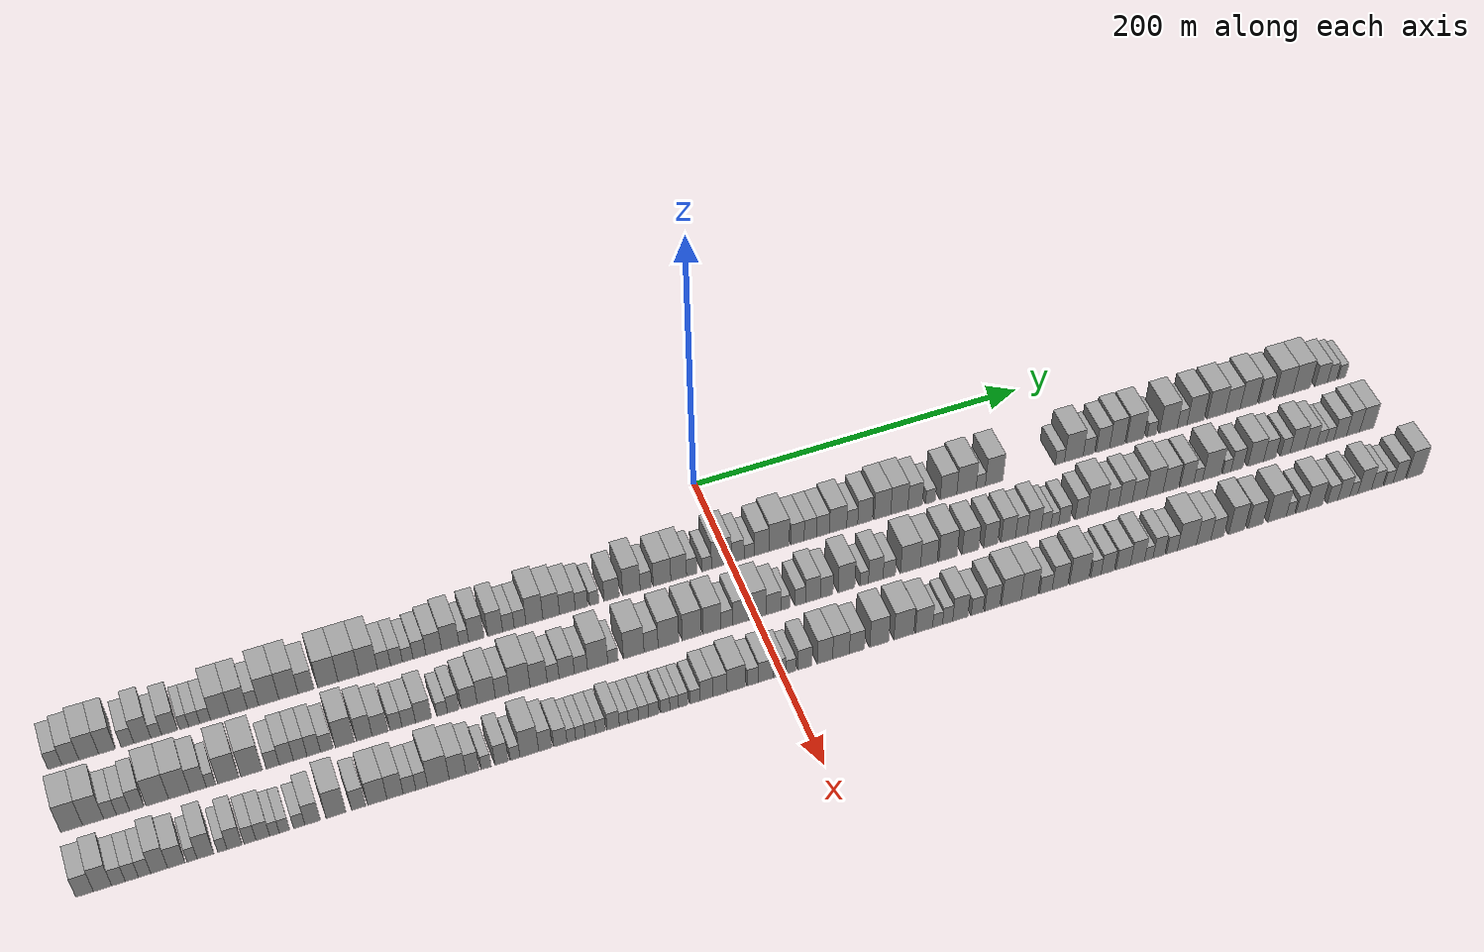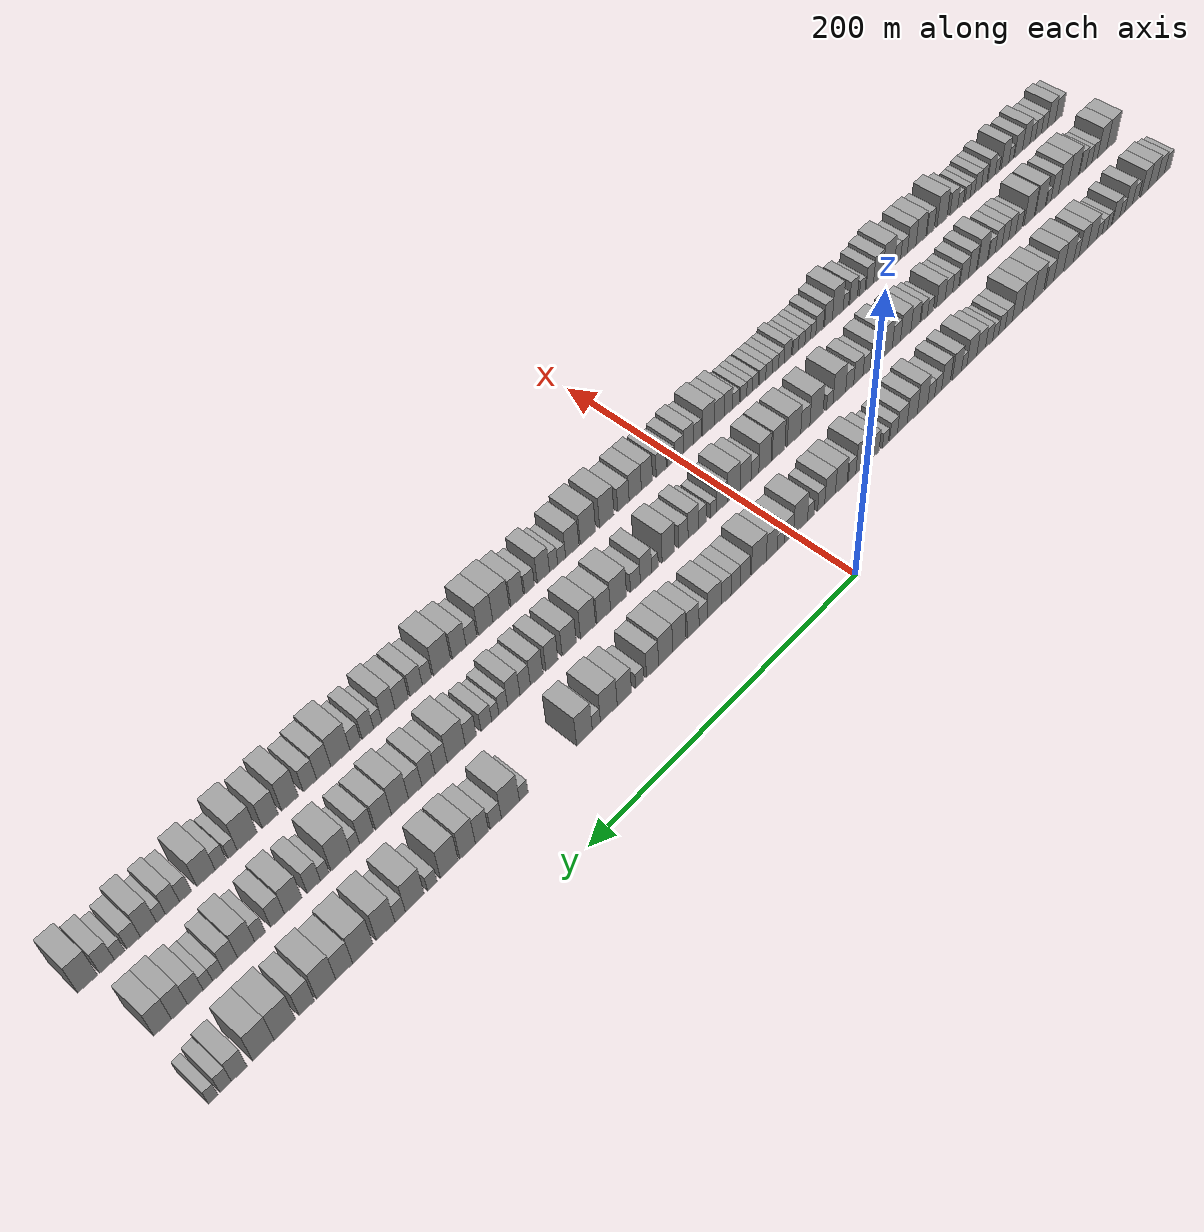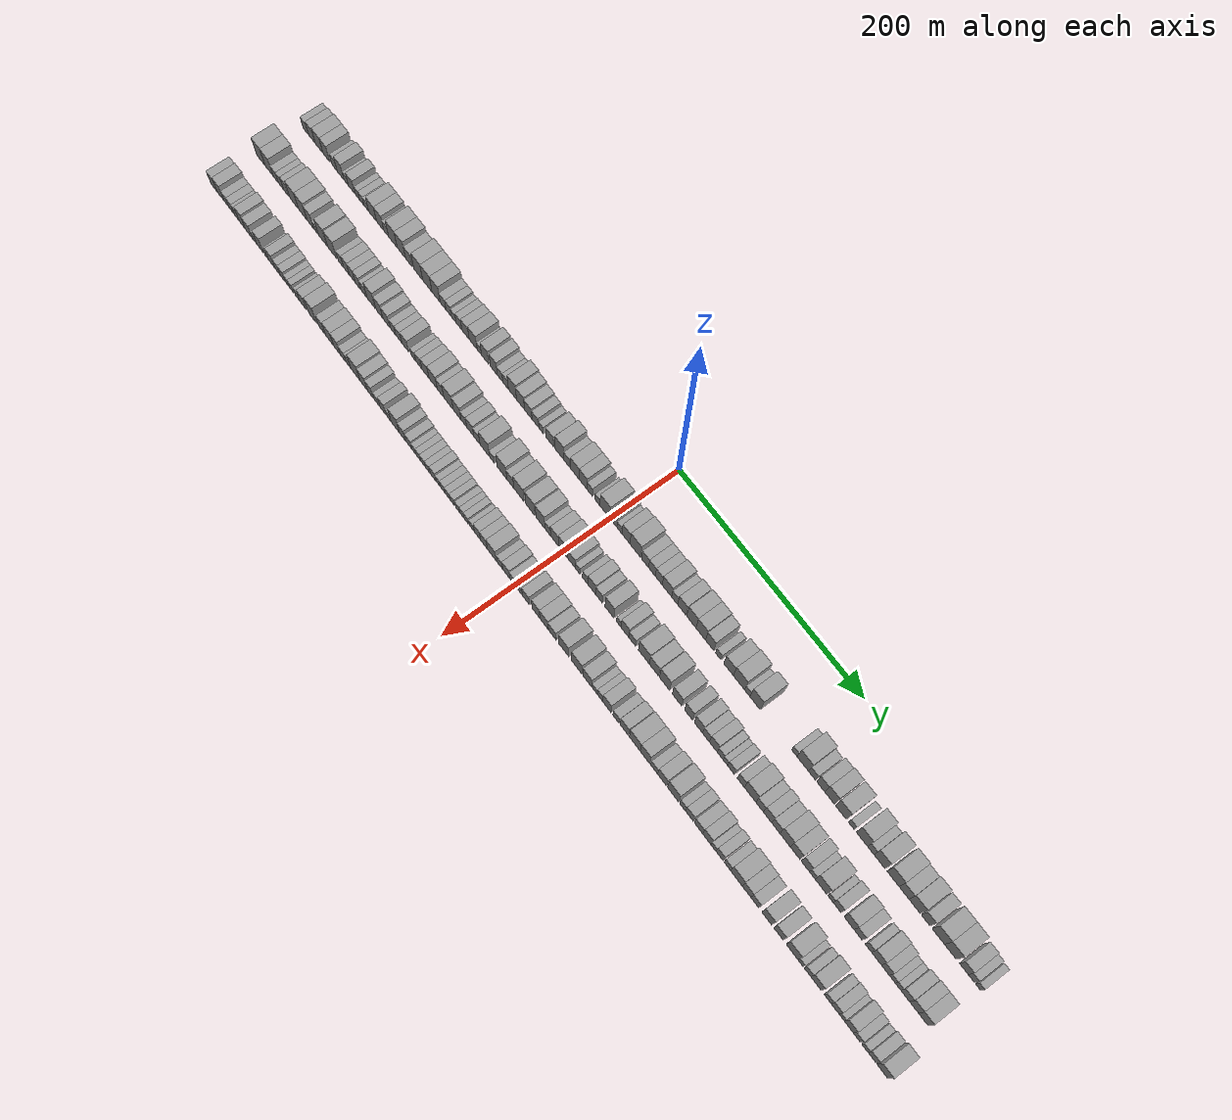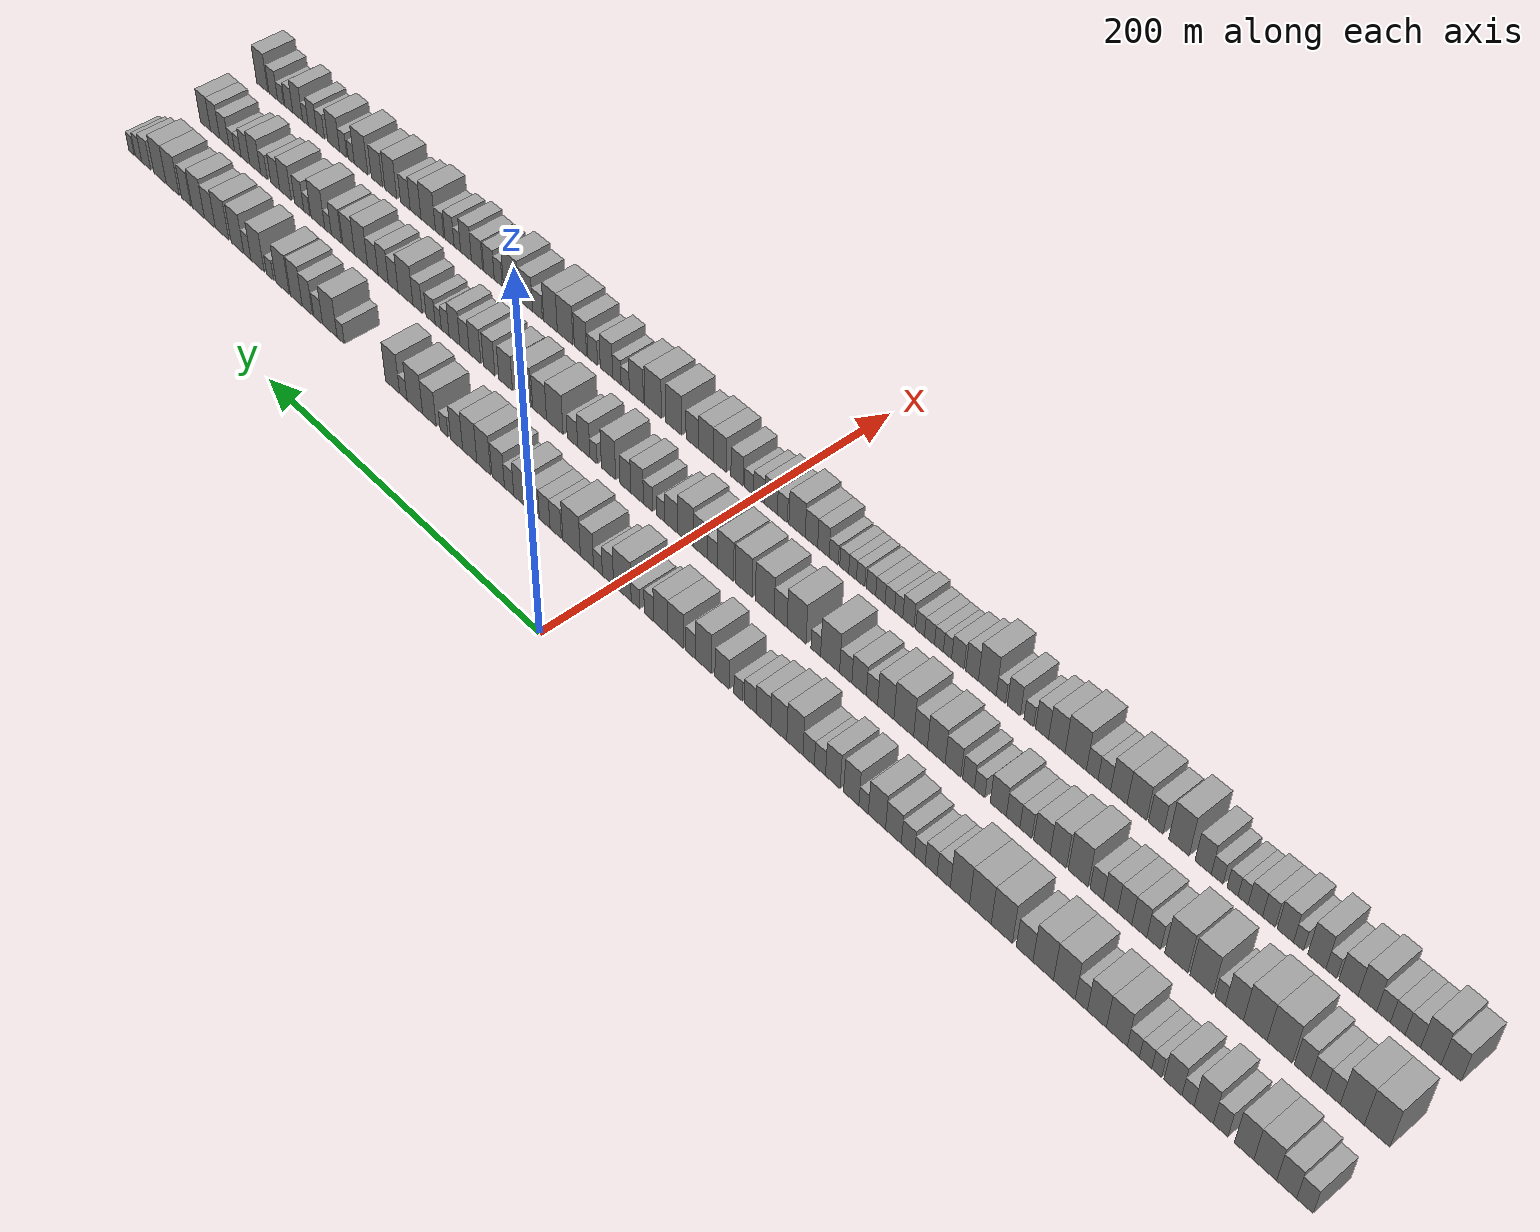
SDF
<sdf version="1.6">
 <world name="default">
  <scene>
   <sky><clouds><speed>12</speed></clouds></sky>
   <ambient>0.4 0.4 0.4 1</ambient>
   <background>0.7 0.7 0.7 1</background>
   <shadows>1</shadows>
  </scene>
  <gravity>0 0 -9.8066</gravity>
  <magnetic_field>6e-06 2.3e-05 -4.2e-05</magnetic_field>
  <physics default="0" name="default_physics" type="ode">
   <ode>
    <solver>
     <type>quick</type>
     <iters>10</iters>
     <sor>1.0</sor>
     <use_dynamic_moi_rescaling>0</use_dynamic_moi_rescaling>
    </solver>
    <constraints>
     <cfm>0</cfm>
     <erp>0.2</erp>
     <contact_max_correcting_vel>100</contact_max_correcting_vel>
     <contact_surface_layer>0.001</contact_surface_layer>
    </constraints>
   </ode>
   <max_step_size>0.004</max_step_size>
   <real_time_factor>1</real_time_factor>
   <real_time_update_rate>250</real_time_update_rate>
  </physics>
  <light name="sun" type="directional">
   <pose>0 0 10 0 0 0</pose>
   <diffuse>0.8 0.8 0.8 1</diffuse>
   <specular>0.2 0.2 0.2 1</specular>
   <attenuation>
    <range>1000</range>
    <constant>0.9</constant>
    <linear>0.01</linear>
    <quadratic>0.001</quadratic>
   </attenuation>
   <direction>-0.5 0.1 -0.9</direction>
  </light>
  <model name="building_1">
   <static>1</static>
   <pose>50.0000 -375.3287 0 0.000000 0.000000 0.000000</pose>
   <link name="link">
    <pose>0 0 7.50 0 0 0</pose>
    <collision name="collision"><geometry><box><size>20.0000 7.3426 15.0000</size></box></geometry></collision>
    <visual name="visual">
     <cast_shadows>0</cast_shadows>
     <geometry><box><size>20.0000 7.3426 15.0000</size></box></geometry>
     <material>
      <script>
       <uri>model://grey_wall/materials/scripts</uri>
       <uri>model://grey_wall/materials/textures</uri>
       <name>vrc/grey_wall</name>
      </script>
     </material>
    </visual>
   </link>
  </model>
  <model name="building_2">
   <static>1</static>
   <pose>50.0000 -367.1831 0 0.000000 0.000000 0.000000</pose>
   <link name="link">
    <pose>0 0 9.00 0 0 0</pose>
    <collision name="collision"><geometry><box><size>20.0000 8.9486 18.0000</size></box></geometry></collision>
    <visual name="visual">
     <cast_shadows>0</cast_shadows>
     <geometry><box><size>20.0000 8.9486 18.0000</size></box></geometry>
     <material>
      <script>
       <uri>model://grey_wall/materials/scripts</uri>
       <uri>model://grey_wall/materials/textures</uri>
       <name>vrc/grey_wall</name>
      </script>
     </material>
    </visual>
   </link>
  </model>
  <model name="building_3">
   <static>1</static>
   <pose>50.0000 -357.5547 0 0.000000 0.000000 0.000000</pose>
   <link name="link">
    <pose>0 0 10.50 0 0 0</pose>
    <collision name="collision"><geometry><box><size>20.0000 10.3081 21.0000</size></box></geometry></collision>
    <visual name="visual">
     <cast_shadows>0</cast_shadows>
     <geometry><box><size>20.0000 10.3081 21.0000</size></box></geometry>
     <material>
      <script>
       <uri>model://grey_wall/materials/scripts</uri>
       <uri>model://grey_wall/materials/textures</uri>
       <name>vrc/grey_wall</name>
      </script>
     </material>
    </visual>
   </link>
  </model>
  <model name="building_4">
   <static>1</static>
   <pose>50.0000 -347.9794 0 0.000000 0.000000 0.000000</pose>
   <link name="link">
    <pose>0 0 10.50 0 0 0</pose>
    <collision name="collision"><geometry><box><size>20.0000 8.8426 21.0000</size></box></geometry></collision>
    <visual name="visual">
     <cast_shadows>0</cast_shadows>
     <geometry><box><size>20.0000 8.8426 21.0000</size></box></geometry>
     <material>
      <script>
       <uri>model://grey_wall/materials/scripts</uri>
       <uri>model://grey_wall/materials/textures</uri>
       <name>vrc/grey_wall</name>
      </script>
     </material>
    </visual>
   </link>
  </model>
  <model name="building_5">
   <static>1</static>
   <pose>50.0000 -337.1684 0 0.000000 0.000000 0.000000</pose>
   <link name="link">
    <pose>0 0 7.50 0 0 0</pose>
    <collision name="collision"><geometry><box><size>20.0000 6.7795 15.0000</size></box></geometry></collision>
    <visual name="visual">
     <cast_shadows>0</cast_shadows>
     <geometry><box><size>20.0000 6.7795 15.0000</size></box></geometry>
     <material>
      <script>
       <uri>model://grey_wall/materials/scripts</uri>
       <uri>model://grey_wall/materials/textures</uri>
       <name>vrc/grey_wall</name>
      </script>
     </material>
    </visual>
   </link>
  </model>
  <model name="building_6">
   <static>1</static>
   <pose>50.0000 -329.2807 0 0.000000 0.000000 0.000000</pose>
   <link name="link">
    <pose>0 0 10.50 0 0 0</pose>
    <collision name="collision"><geometry><box><size>20.0000 8.9958 21.0000</size></box></geometry></collision>
    <visual name="visual">
     <cast_shadows>0</cast_shadows>
     <geometry><box><size>20.0000 8.9958 21.0000</size></box></geometry>
     <material>
      <script>
       <uri>model://grey_wall/materials/scripts</uri>
       <uri>model://grey_wall/materials/textures</uri>
       <name>vrc/grey_wall</name>
      </script>
     </material>
    </visual>
   </link>
  </model>
  <model name="building_7">
   <static>1</static>
   <pose>50.0000 -321.9267 0 0.000000 0.000000 0.000000</pose>
   <link name="link">
    <pose>0 0 6.00 0 0 0</pose>
    <collision name="collision"><geometry><box><size>20.0000 5.7122 12.0000</size></box></geometry></collision>
    <visual name="visual">
     <cast_shadows>0</cast_shadows>
     <geometry><box><size>20.0000 5.7122 12.0000</size></box></geometry>
     <material>
      <script>
       <uri>model://grey_wall/materials/scripts</uri>
       <uri>model://grey_wall/materials/textures</uri>
       <name>vrc/grey_wall</name>
      </script>
     </material>
    </visual>
   </link>
  </model>
  <model name="building_8">
   <static>1</static>
   <pose>50.0000 -314.7755 0 0.000000 0.000000 0.000000</pose>
   <link name="link">
    <pose>0 0 9.00 0 0 0</pose>
    <collision name="collision"><geometry><box><size>20.0000 8.5903 18.0000</size></box></geometry></collision>
    <visual name="visual">
     <cast_shadows>0</cast_shadows>
     <geometry><box><size>20.0000 8.5903 18.0000</size></box></geometry>
     <material>
      <script>
       <uri>model://grey_wall/materials/scripts</uri>
       <uri>model://grey_wall/materials/textures</uri>
       <name>vrc/grey_wall</name>
      </script>
     </material>
    </visual>
   </link>
  </model>
  <model name="building_9">
   <static>1</static>
   <pose>50.0000 -307.0648 0 0.000000 0.000000 0.000000</pose>
   <link name="link">
    <pose>0 0 6.00 0 0 0</pose>
    <collision name="collision"><geometry><box><size>20.0000 4.8309 12.0000</size></box></geometry></collision>
    <visual name="visual">
     <cast_shadows>0</cast_shadows>
     <geometry><box><size>20.0000 4.8309 12.0000</size></box></geometry>
     <material>
      <script>
       <uri>model://grey_wall/materials/scripts</uri>
       <uri>model://grey_wall/materials/textures</uri>
       <name>vrc/grey_wall</name>
      </script>
     </material>
    </visual>
   </link>
  </model>
  <model name="building_10">
   <static>1</static>
   <pose>50.0000 -301.6668 0 0.000000 0.000000 0.000000</pose>
   <link name="link">
    <pose>0 0 6.00 0 0 0</pose>
    <collision name="collision"><geometry><box><size>20.0000 5.9651 12.0000</size></box></geometry></collision>
    <visual name="visual">
     <cast_shadows>0</cast_shadows>
     <geometry><box><size>20.0000 5.9651 12.0000</size></box></geometry>
     <material>
      <script>
       <uri>model://grey_wall/materials/scripts</uri>
       <uri>model://grey_wall/materials/textures</uri>
       <name>vrc/grey_wall</name>
      </script>
     </material>
    </visual>
   </link>
  </model>
  <model name="building_11">
   <static>1</static>
   <pose>50.0000 -295.7487 0 0.000000 0.000000 0.000000</pose>
   <link name="link">
    <pose>0 0 6.00 0 0 0</pose>
    <collision name="collision"><geometry><box><size>20.0000 5.8713 12.0000</size></box></geometry></collision>
    <visual name="visual">
     <cast_shadows>0</cast_shadows>
     <geometry><box><size>20.0000 5.8713 12.0000</size></box></geometry>
     <material>
      <script>
       <uri>model://grey_wall/materials/scripts</uri>
       <uri>model://grey_wall/materials/textures</uri>
       <name>vrc/grey_wall</name>
      </script>
     </material>
    </visual>
   </link>
  </model>
  <model name="building_12">
   <static>1</static>
   <pose>50.0000 -287.6685 0 0.000000 0.000000 0.000000</pose>
   <link name="link">
    <pose>0 0 10.50 0 0 0</pose>
    <collision name="collision"><geometry><box><size>20.0000 10.2891 21.0000</size></box></geometry></collision>
    <visual name="visual">
     <cast_shadows>0</cast_shadows>
     <geometry><box><size>20.0000 10.2891 21.0000</size></box></geometry>
     <material>
      <script>
       <uri>model://grey_wall/materials/scripts</uri>
       <uri>model://grey_wall/materials/textures</uri>
       <name>vrc/grey_wall</name>
      </script>
     </material>
    </visual>
   </link>
  </model>
  <model name="building_13">
   <static>1</static>
   <pose>50.0000 -277.7995 0 0.000000 0.000000 0.000000</pose>
   <link name="link">
    <pose>0 0 10.50 0 0 0</pose>
    <collision name="collision"><geometry><box><size>20.0000 9.4488 21.0000</size></box></geometry></collision>
    <visual name="visual">
     <cast_shadows>0</cast_shadows>
     <geometry><box><size>20.0000 9.4488 21.0000</size></box></geometry>
     <material>
      <script>
       <uri>model://grey_wall/materials/scripts</uri>
       <uri>model://grey_wall/materials/textures</uri>
       <name>vrc/grey_wall</name>
      </script>
     </material>
    </visual>
   </link>
  </model>
  <model name="building_14">
   <static>1</static>
   <pose>50.0000 -270.0500 0 0.000000 0.000000 0.000000</pose>
   <link name="link">
    <pose>0 0 7.50 0 0 0</pose>
    <collision name="collision"><geometry><box><size>20.0000 6.0503 15.0000</size></box></geometry></collision>
    <visual name="visual">
     <cast_shadows>0</cast_shadows>
     <geometry><box><size>20.0000 6.0503 15.0000</size></box></geometry>
     <material>
      <script>
       <uri>model://grey_wall/materials/scripts</uri>
       <uri>model://grey_wall/materials/textures</uri>
       <name>vrc/grey_wall</name>
      </script>
     </material>
    </visual>
   </link>
  </model>
  <model name="building_15">
   <static>1</static>
   <pose>50.0000 -261.5179 0 0.000000 0.000000 0.000000</pose>
   <link name="link">
    <pose>0 0 12.00 0 0 0</pose>
    <collision name="collision"><geometry><box><size>20.0000 11.0138 24.0000</size></box></geometry></collision>
    <visual name="visual">
     <cast_shadows>0</cast_shadows>
     <geometry><box><size>20.0000 11.0138 24.0000</size></box></geometry>
     <material>
      <script>
       <uri>model://grey_wall/materials/scripts</uri>
       <uri>model://grey_wall/materials/textures</uri>
       <name>vrc/grey_wall</name>
      </script>
     </material>
    </visual>
   </link>
  </model>
  <model name="building_16">
   <static>1</static>
   <pose>50.0000 -250.7442 0 0.000000 0.000000 0.000000</pose>
   <link name="link">
    <pose>0 0 12.00 0 0 0</pose>
    <collision name="collision"><geometry><box><size>20.0000 10.5337 24.0000</size></box></geometry></collision>
    <visual name="visual">
     <cast_shadows>0</cast_shadows>
     <geometry><box><size>20.0000 10.5337 24.0000</size></box></geometry>
     <material>
      <script>
       <uri>model://grey_wall/materials/scripts</uri>
       <uri>model://grey_wall/materials/textures</uri>
       <name>vrc/grey_wall</name>
      </script>
     </material>
    </visual>
   </link>
  </model>
  <model name="building_17">
   <static>1</static>
   <pose>50.0000 -241.1587 0 0.000000 0.000000 0.000000</pose>
   <link name="link">
    <pose>0 0 9.00 0 0 0</pose>
    <collision name="collision"><geometry><box><size>20.0000 8.6373 18.0000</size></box></geometry></collision>
    <visual name="visual">
     <cast_shadows>0</cast_shadows>
     <geometry><box><size>20.0000 8.6373 18.0000</size></box></geometry>
     <material>
      <script>
       <uri>model://grey_wall/materials/scripts</uri>
       <uri>model://grey_wall/materials/textures</uri>
       <name>vrc/grey_wall</name>
      </script>
     </material>
    </visual>
   </link>
  </model>
  <model name="building_18">
   <static>1</static>
   <pose>50.0000 -229.2671 0 0.000000 0.000000 0.000000</pose>
   <link name="link">
    <pose>0 0 12.00 0 0 0</pose>
    <collision name="collision"><geometry><box><size>20.0000 11.1459 24.0000</size></box></geometry></collision>
    <visual name="visual">
     <cast_shadows>0</cast_shadows>
     <geometry><box><size>20.0000 11.1459 24.0000</size></box></geometry>
     <material>
      <script>
       <uri>model://grey_wall/materials/scripts</uri>
       <uri>model://grey_wall/materials/textures</uri>
       <name>vrc/grey_wall</name>
      </script>
     </material>
    </visual>
   </link>
  </model>
  <model name="building_19">
   <static>1</static>
   <pose>50.0000 -217.9231 0 0.000000 0.000000 0.000000</pose>
   <link name="link">
    <pose>0 0 12.00 0 0 0</pose>
    <collision name="collision"><geometry><box><size>20.0000 11.5422 24.0000</size></box></geometry></collision>
    <visual name="visual">
     <cast_shadows>0</cast_shadows>
     <geometry><box><size>20.0000 11.5422 24.0000</size></box></geometry>
     <material>
      <script>
       <uri>model://grey_wall/materials/scripts</uri>
       <uri>model://grey_wall/materials/textures</uri>
       <name>vrc/grey_wall</name>
      </script>
     </material>
    </visual>
   </link>
  </model>
  <model name="building_20">
   <static>1</static>
   <pose>50.0000 -207.0150 0 0.000000 0.000000 0.000000</pose>
   <link name="link">
    <pose>0 0 12.00 0 0 0</pose>
    <collision name="collision"><geometry><box><size>20.0000 10.2741 24.0000</size></box></geometry></collision>
    <visual name="visual">
     <cast_shadows>0</cast_shadows>
     <geometry><box><size>20.0000 10.2741 24.0000</size></box></geometry>
     <material>
      <script>
       <uri>model://grey_wall/materials/scripts</uri>
       <uri>model://grey_wall/materials/textures</uri>
       <name>vrc/grey_wall</name>
      </script>
     </material>
    </visual>
   </link>
  </model>
  <model name="building_21">
   <static>1</static>
   <pose>50.0000 -198.2730 0 0.000000 0.000000 0.000000</pose>
   <link name="link">
    <pose>0 0 7.50 0 0 0</pose>
    <collision name="collision"><geometry><box><size>20.0000 7.2099 15.0000</size></box></geometry></collision>
    <visual name="visual">
     <cast_shadows>0</cast_shadows>
     <geometry><box><size>20.0000 7.2099 15.0000</size></box></geometry>
     <material>
      <script>
       <uri>model://grey_wall/materials/scripts</uri>
       <uri>model://grey_wall/materials/textures</uri>
       <name>vrc/grey_wall</name>
      </script>
     </material>
    </visual>
   </link>
  </model>
  <model name="building_22">
   <static>1</static>
   <pose>50.0000 -191.3809 0 0.000000 0.000000 0.000000</pose>
   <link name="link">
    <pose>0 0 7.50 0 0 0</pose>
    <collision name="collision"><geometry><box><size>20.0000 6.5743 15.0000</size></box></geometry></collision>
    <visual name="visual">
     <cast_shadows>0</cast_shadows>
     <geometry><box><size>20.0000 6.5743 15.0000</size></box></geometry>
     <material>
      <script>
       <uri>model://grey_wall/materials/scripts</uri>
       <uri>model://grey_wall/materials/textures</uri>
       <name>vrc/grey_wall</name>
      </script>
     </material>
    </visual>
   </link>
  </model>
  <model name="building_23">
   <static>1</static>
   <pose>50.0000 -185.1483 0 0.000000 0.000000 0.000000</pose>
   <link name="link">
    <pose>0 0 6.00 0 0 0</pose>
    <collision name="collision"><geometry><box><size>20.0000 5.8909 12.0000</size></box></geometry></collision>
    <visual name="visual">
     <cast_shadows>0</cast_shadows>
     <geometry><box><size>20.0000 5.8909 12.0000</size></box></geometry>
     <material>
      <script>
       <uri>model://grey_wall/materials/scripts</uri>
       <uri>model://grey_wall/materials/textures</uri>
       <name>vrc/grey_wall</name>
      </script>
     </material>
    </visual>
   </link>
  </model>
  <model name="building_24">
   <static>1</static>
   <pose>50.0000 -178.5799 0 0.000000 0.000000 0.000000</pose>
   <link name="link">
    <pose>0 0 7.50 0 0 0</pose>
    <collision name="collision"><geometry><box><size>20.0000 7.2459 15.0000</size></box></geometry></collision>
    <visual name="visual">
     <cast_shadows>0</cast_shadows>
     <geometry><box><size>20.0000 7.2459 15.0000</size></box></geometry>
     <material>
      <script>
       <uri>model://grey_wall/materials/scripts</uri>
       <uri>model://grey_wall/materials/textures</uri>
       <name>vrc/grey_wall</name>
      </script>
     </material>
    </visual>
   </link>
  </model>
  <model name="building_25">
   <static>1</static>
   <pose>50.0000 -170.5473 0 0.000000 0.000000 0.000000</pose>
   <link name="link">
    <pose>0 0 9.00 0 0 0</pose>
    <collision name="collision"><geometry><box><size>20.0000 8.8192 18.0000</size></box></geometry></collision>
    <visual name="visual">
     <cast_shadows>0</cast_shadows>
     <geometry><box><size>20.0000 8.8192 18.0000</size></box></geometry>
     <material>
      <script>
       <uri>model://grey_wall/materials/scripts</uri>
       <uri>model://grey_wall/materials/textures</uri>
       <name>vrc/grey_wall</name>
      </script>
     </material>
    </visual>
   </link>
  </model>
  <model name="building_26">
   <static>1</static>
   <pose>50.0000 -161.2789 0 0.000000 0.000000 0.000000</pose>
   <link name="link">
    <pose>0 0 10.50 0 0 0</pose>
    <collision name="collision"><geometry><box><size>20.0000 9.7175 21.0000</size></box></geometry></collision>
    <visual name="visual">
     <cast_shadows>0</cast_shadows>
     <geometry><box><size>20.0000 9.7175 21.0000</size></box></geometry>
     <material>
      <script>
       <uri>model://grey_wall/materials/scripts</uri>
       <uri>model://grey_wall/materials/textures</uri>
       <name>vrc/grey_wall</name>
      </script>
     </material>
    </visual>
   </link>
  </model>
  <model name="building_27">
   <static>1</static>
   <pose>50.0000 -153.7344 0 0.000000 0.000000 0.000000</pose>
   <link name="link">
    <pose>0 0 6.00 0 0 0</pose>
    <collision name="collision"><geometry><box><size>20.0000 5.3715 12.0000</size></box></geometry></collision>
    <visual name="visual">
     <cast_shadows>0</cast_shadows>
     <geometry><box><size>20.0000 5.3715 12.0000</size></box></geometry>
     <material>
      <script>
       <uri>model://grey_wall/materials/scripts</uri>
       <uri>model://grey_wall/materials/textures</uri>
       <name>vrc/grey_wall</name>
      </script>
     </material>
    </visual>
   </link>
  </model>
  <model name="building_28">
   <static>1</static>
   <pose>50.0000 -146.6572 0 0.000000 0.000000 0.000000</pose>
   <link name="link">
    <pose>0 0 10.50 0 0 0</pose>
    <collision name="collision"><geometry><box><size>20.0000 8.7830 21.0000</size></box></geometry></collision>
    <visual name="visual">
     <cast_shadows>0</cast_shadows>
     <geometry><box><size>20.0000 8.7830 21.0000</size></box></geometry>
     <material>
      <script>
       <uri>model://grey_wall/materials/scripts</uri>
       <uri>model://grey_wall/materials/textures</uri>
       <name>vrc/grey_wall</name>
      </script>
     </material>
    </visual>
   </link>
  </model>
  <model name="building_29">
   <static>1</static>
   <pose>50.0000 -136.0316 0 0.000000 0.000000 0.000000</pose>
   <link name="link">
    <pose>0 0 10.50 0 0 0</pose>
    <collision name="collision"><geometry><box><size>20.0000 8.4683 21.0000</size></box></geometry></collision>
    <visual name="visual">
     <cast_shadows>0</cast_shadows>
     <geometry><box><size>20.0000 8.4683 21.0000</size></box></geometry>
     <material>
      <script>
       <uri>model://grey_wall/materials/scripts</uri>
       <uri>model://grey_wall/materials/textures</uri>
       <name>vrc/grey_wall</name>
      </script>
     </material>
    </visual>
   </link>
  </model>
  <model name="building_30">
   <static>1</static>
   <pose>50.0000 -128.5220 0 0.000000 0.000000 0.000000</pose>
   <link name="link">
    <pose>0 0 7.50 0 0 0</pose>
    <collision name="collision"><geometry><box><size>20.0000 6.5510 15.0000</size></box></geometry></collision>
    <visual name="visual">
     <cast_shadows>0</cast_shadows>
     <geometry><box><size>20.0000 6.5510 15.0000</size></box></geometry>
     <material>
      <script>
       <uri>model://grey_wall/materials/scripts</uri>
       <uri>model://grey_wall/materials/textures</uri>
       <name>vrc/grey_wall</name>
      </script>
     </material>
    </visual>
   </link>
  </model>
  <model name="building_31">
   <static>1</static>
   <pose>50.0000 -121.9034 0 0.000000 0.000000 0.000000</pose>
   <link name="link">
    <pose>0 0 7.50 0 0 0</pose>
    <collision name="collision"><geometry><box><size>20.0000 6.6861 15.0000</size></box></geometry></collision>
    <visual name="visual">
     <cast_shadows>0</cast_shadows>
     <geometry><box><size>20.0000 6.6861 15.0000</size></box></geometry>
     <material>
      <script>
       <uri>model://grey_wall/materials/scripts</uri>
       <uri>model://grey_wall/materials/textures</uri>
       <name>vrc/grey_wall</name>
      </script>
     </material>
    </visual>
   </link>
  </model>
  <model name="building_32">
   <static>1</static>
   <pose>50.0000 -113.7323 0 0.000000 0.000000 0.000000</pose>
   <link name="link">
    <pose>0 0 12.00 0 0 0</pose>
    <collision name="collision"><geometry><box><size>20.0000 9.6560 24.0000</size></box></geometry></collision>
    <visual name="visual">
     <cast_shadows>0</cast_shadows>
     <geometry><box><size>20.0000 9.6560 24.0000</size></box></geometry>
     <material>
      <script>
       <uri>model://grey_wall/materials/scripts</uri>
       <uri>model://grey_wall/materials/textures</uri>
       <name>vrc/grey_wall</name>
      </script>
     </material>
    </visual>
   </link>
  </model>
  <model name="building_33">
   <static>1</static>
   <pose>50.0000 -104.1576 0 0.000000 0.000000 0.000000</pose>
   <link name="link">
    <pose>0 0 10.50 0 0 0</pose>
    <collision name="collision"><geometry><box><size>20.0000 9.4935 21.0000</size></box></geometry></collision>
    <visual name="visual">
     <cast_shadows>0</cast_shadows>
     <geometry><box><size>20.0000 9.4935 21.0000</size></box></geometry>
     <material>
      <script>
       <uri>model://grey_wall/materials/scripts</uri>
       <uri>model://grey_wall/materials/textures</uri>
       <name>vrc/grey_wall</name>
      </script>
     </material>
    </visual>
   </link>
  </model>
  <model name="building_34">
   <static>1</static>
   <pose>50.0000 -94.9285 0 0.000000 0.000000 0.000000</pose>
   <link name="link">
    <pose>0 0 9.00 0 0 0</pose>
    <collision name="collision"><geometry><box><size>20.0000 8.9646 18.0000</size></box></geometry></collision>
    <visual name="visual">
     <cast_shadows>0</cast_shadows>
     <geometry><box><size>20.0000 8.9646 18.0000</size></box></geometry>
     <material>
      <script>
       <uri>model://grey_wall/materials/scripts</uri>
       <uri>model://grey_wall/materials/textures</uri>
       <name>vrc/grey_wall</name>
      </script>
     </material>
    </visual>
   </link>
  </model>
  <model name="building_35">
   <static>1</static>
   <pose>50.0000 -86.8343 0 0.000000 0.000000 0.000000</pose>
   <link name="link">
    <pose>0 0 7.50 0 0 0</pose>
    <collision name="collision"><geometry><box><size>20.0000 7.2239 15.0000</size></box></geometry></collision>
    <visual name="visual">
     <cast_shadows>0</cast_shadows>
     <geometry><box><size>20.0000 7.2239 15.0000</size></box></geometry>
     <material>
      <script>
       <uri>model://grey_wall/materials/scripts</uri>
       <uri>model://grey_wall/materials/textures</uri>
       <name>vrc/grey_wall</name>
      </script>
     </material>
    </visual>
   </link>
  </model>
  <model name="building_36">
   <static>1</static>
   <pose>50.0000 -79.5153 0 0.000000 0.000000 0.000000</pose>
   <link name="link">
    <pose>0 0 6.00 0 0 0</pose>
    <collision name="collision"><geometry><box><size>20.0000 5.4139 12.0000</size></box></geometry></collision>
    <visual name="visual">
     <cast_shadows>0</cast_shadows>
     <geometry><box><size>20.0000 5.4139 12.0000</size></box></geometry>
     <material>
      <script>
       <uri>model://grey_wall/materials/scripts</uri>
       <uri>model://grey_wall/materials/textures</uri>
       <name>vrc/grey_wall</name>
      </script>
     </material>
    </visual>
   </link>
  </model>
  <model name="building_37">
   <static>1</static>
   <pose>50.0000 -69.4251 0 0.000000 0.000000 0.000000</pose>
   <link name="link">
    <pose>0 0 9.00 0 0 0</pose>
    <collision name="collision"><geometry><box><size>20.0000 8.7666 18.0000</size></box></geometry></collision>
    <visual name="visual">
     <cast_shadows>0</cast_shadows>
     <geometry><box><size>20.0000 8.7666 18.0000</size></box></geometry>
     <material>
      <script>
       <uri>model://grey_wall/materials/scripts</uri>
       <uri>model://grey_wall/materials/textures</uri>
       <name>vrc/grey_wall</name>
      </script>
     </material>
    </visual>
   </link>
  </model>
  <model name="building_38">
   <static>1</static>
   <pose>50.0000 -57.9924 0 0.000000 0.000000 0.000000</pose>
   <link name="link">
    <pose>0 0 12.00 0 0 0</pose>
    <collision name="collision"><geometry><box><size>20.0000 10.0988 24.0000</size></box></geometry></collision>
    <visual name="visual">
     <cast_shadows>0</cast_shadows>
     <geometry><box><size>20.0000 10.0988 24.0000</size></box></geometry>
     <material>
      <script>
       <uri>model://grey_wall/materials/scripts</uri>
       <uri>model://grey_wall/materials/textures</uri>
       <name>vrc/grey_wall</name>
      </script>
     </material>
    </visual>
   </link>
  </model>
  <model name="building_39">
   <static>1</static>
   <pose>50.0000 -49.6434 0 0.000000 0.000000 0.000000</pose>
   <link name="link">
    <pose>0 0 7.50 0 0 0</pose>
    <collision name="collision"><geometry><box><size>20.0000 6.5993 15.0000</size></box></geometry></collision>
    <visual name="visual">
     <cast_shadows>0</cast_shadows>
     <geometry><box><size>20.0000 6.5993 15.0000</size></box></geometry>
     <material>
      <script>
       <uri>model://grey_wall/materials/scripts</uri>
       <uri>model://grey_wall/materials/textures</uri>
       <name>vrc/grey_wall</name>
      </script>
     </material>
    </visual>
   </link>
  </model>
  <model name="building_40">
   <static>1</static>
   <pose>50.0000 -40.2139 0 0.000000 0.000000 0.000000</pose>
   <link name="link">
    <pose>0 0 10.50 0 0 0</pose>
    <collision name="collision"><geometry><box><size>20.0000 10.2598 21.0000</size></box></geometry></collision>
    <visual name="visual">
     <cast_shadows>0</cast_shadows>
     <geometry><box><size>20.0000 10.2598 21.0000</size></box></geometry>
     <material>
      <script>
       <uri>model://grey_wall/materials/scripts</uri>
       <uri>model://grey_wall/materials/textures</uri>
       <name>vrc/grey_wall</name>
      </script>
     </material>
    </visual>
   </link>
  </model>
  <model name="building_41">
   <static>1</static>
   <pose>50.0000 -30.4918 0 0.000000 0.000000 0.000000</pose>
   <link name="link">
    <pose>0 0 10.50 0 0 0</pose>
    <collision name="collision"><geometry><box><size>20.0000 9.1844 21.0000</size></box></geometry></collision>
    <visual name="visual">
     <cast_shadows>0</cast_shadows>
     <geometry><box><size>20.0000 9.1844 21.0000</size></box></geometry>
     <material>
      <script>
       <uri>model://grey_wall/materials/scripts</uri>
       <uri>model://grey_wall/materials/textures</uri>
       <name>vrc/grey_wall</name>
      </script>
     </material>
    </visual>
   </link>
  </model>
  <model name="building_42">
   <static>1</static>
   <pose>50.0000 -22.8760 0 0.000000 0.000000 0.000000</pose>
   <link name="link">
    <pose>0 0 7.50 0 0 0</pose>
    <collision name="collision"><geometry><box><size>20.0000 6.0470 15.0000</size></box></geometry></collision>
    <visual name="visual">
     <cast_shadows>0</cast_shadows>
     <geometry><box><size>20.0000 6.0470 15.0000</size></box></geometry>
     <material>
      <script>
       <uri>model://grey_wall/materials/scripts</uri>
       <uri>model://grey_wall/materials/textures</uri>
       <name>vrc/grey_wall</name>
      </script>
     </material>
    </visual>
   </link>
  </model>
  <model name="building_43">
   <static>1</static>
   <pose>50.0000 -14.0464 0 0.000000 0.000000 0.000000</pose>
   <link name="link">
    <pose>0 0 6.00 0 0 0</pose>
    <collision name="collision"><geometry><box><size>20.0000 5.6122 12.0000</size></box></geometry></collision>
    <visual name="visual">
     <cast_shadows>0</cast_shadows>
     <geometry><box><size>20.0000 5.6122 12.0000</size></box></geometry>
     <material>
      <script>
       <uri>model://grey_wall/materials/scripts</uri>
       <uri>model://grey_wall/materials/textures</uri>
       <name>vrc/grey_wall</name>
      </script>
     </material>
    </visual>
   </link>
  </model>
  <model name="building_44">
   <static>1</static>
   <pose>50.0000 -5.3865 0 0.000000 0.000000 0.000000</pose>
   <link name="link">
    <pose>0 0 12.00 0 0 0</pose>
    <collision name="collision"><geometry><box><size>20.0000 11.7078 24.0000</size></box></geometry></collision>
    <visual name="visual">
     <cast_shadows>0</cast_shadows>
     <geometry><box><size>20.0000 11.7078 24.0000</size></box></geometry>
     <material>
      <script>
       <uri>model://grey_wall/materials/scripts</uri>
       <uri>model://grey_wall/materials/textures</uri>
       <name>vrc/grey_wall</name>
      </script>
     </material>
    </visual>
   </link>
  </model>
  <model name="building_45">
   <static>1</static>
   <pose>50.0000 4.2146 0 0.000000 0.000000 0.000000</pose>
   <link name="link">
    <pose>0 0 9.00 0 0 0</pose>
    <collision name="collision"><geometry><box><size>20.0000 7.4943 18.0000</size></box></geometry></collision>
    <visual name="visual">
     <cast_shadows>0</cast_shadows>
     <geometry><box><size>20.0000 7.4943 18.0000</size></box></geometry>
     <material>
      <script>
       <uri>model://grey_wall/materials/scripts</uri>
       <uri>model://grey_wall/materials/textures</uri>
       <name>vrc/grey_wall</name>
      </script>
     </material>
    </visual>
   </link>
  </model>
  <model name="building_46">
   <static>1</static>
   <pose>50.0000 10.9551 0 0.000000 0.000000 0.000000</pose>
   <link name="link">
    <pose>0 0 6.00 0 0 0</pose>
    <collision name="collision"><geometry><box><size>20.0000 5.9868 12.0000</size></box></geometry></collision>
    <visual name="visual">
     <cast_shadows>0</cast_shadows>
     <geometry><box><size>20.0000 5.9868 12.0000</size></box></geometry>
     <material>
      <script>
       <uri>model://grey_wall/materials/scripts</uri>
       <uri>model://grey_wall/materials/textures</uri>
       <name>vrc/grey_wall</name>
      </script>
     </material>
    </visual>
   </link>
  </model>
  <model name="building_47">
   <static>1</static>
   <pose>50.0000 18.4192 0 0.000000 0.000000 0.000000</pose>
   <link name="link">
    <pose>0 0 10.50 0 0 0</pose>
    <collision name="collision"><geometry><box><size>20.0000 8.9415 21.0000</size></box></geometry></collision>
    <visual name="visual">
     <cast_shadows>0</cast_shadows>
     <geometry><box><size>20.0000 8.9415 21.0000</size></box></geometry>
     <material>
      <script>
       <uri>model://grey_wall/materials/scripts</uri>
       <uri>model://grey_wall/materials/textures</uri>
       <name>vrc/grey_wall</name>
      </script>
     </material>
    </visual>
   </link>
  </model>
  <model name="building_48">
   <static>1</static>
   <pose>50.0000 28.8861 0 0.000000 0.000000 0.000000</pose>
   <link name="link">
    <pose>0 0 12.00 0 0 0</pose>
    <collision name="collision"><geometry><box><size>20.0000 11.9924 24.0000</size></box></geometry></collision>
    <visual name="visual">
     <cast_shadows>0</cast_shadows>
     <geometry><box><size>20.0000 11.9924 24.0000</size></box></geometry>
     <material>
      <script>
       <uri>model://grey_wall/materials/scripts</uri>
       <uri>model://grey_wall/materials/textures</uri>
       <name>vrc/grey_wall</name>
      </script>
     </material>
    </visual>
   </link>
  </model>
  <model name="building_49">
   <static>1</static>
   <pose>50.0000 39.8262 0 0.000000 0.000000 0.000000</pose>
   <link name="link">
    <pose>0 0 9.00 0 0 0</pose>
    <collision name="collision"><geometry><box><size>20.0000 7.8877 18.0000</size></box></geometry></collision>
    <visual name="visual">
     <cast_shadows>0</cast_shadows>
     <geometry><box><size>20.0000 7.8877 18.0000</size></box></geometry>
     <material>
      <script>
       <uri>model://grey_wall/materials/scripts</uri>
       <uri>model://grey_wall/materials/textures</uri>
       <name>vrc/grey_wall</name>
      </script>
     </material>
    </visual>
   </link>
  </model>
  <model name="building_50">
   <static>1</static>
   <pose>50.0000 47.4866 0 0.000000 0.000000 0.000000</pose>
   <link name="link">
    <pose>0 0 9.00 0 0 0</pose>
    <collision name="collision"><geometry><box><size>20.0000 7.4331 18.0000</size></box></geometry></collision>
    <visual name="visual">
     <cast_shadows>0</cast_shadows>
     <geometry><box><size>20.0000 7.4331 18.0000</size></box></geometry>
     <material>
      <script>
       <uri>model://grey_wall/materials/scripts</uri>
       <uri>model://grey_wall/materials/textures</uri>
       <name>vrc/grey_wall</name>
      </script>
     </material>
    </visual>
   </link>
  </model>
  <model name="building_51">
   <static>1</static>
   <pose>50.0000 55.0827 0 0.000000 0.000000 0.000000</pose>
   <link name="link">
    <pose>0 0 9.00 0 0 0</pose>
    <collision name="collision"><geometry><box><size>20.0000 7.7591 18.0000</size></box></geometry></collision>
    <visual name="visual">
     <cast_shadows>0</cast_shadows>
     <geometry><box><size>20.0000 7.7591 18.0000</size></box></geometry>
     <material>
      <script>
       <uri>model://grey_wall/materials/scripts</uri>
       <uri>model://grey_wall/materials/textures</uri>
       <name>vrc/grey_wall</name>
      </script>
     </material>
    </visual>
   </link>
  </model>
  <model name="building_52">
   <static>1</static>
   <pose>50.0000 64.1547 0 0.000000 0.000000 0.000000</pose>
   <link name="link">
    <pose>0 0 10.50 0 0 0</pose>
    <collision name="collision"><geometry><box><size>20.0000 10.3849 21.0000</size></box></geometry></collision>
    <visual name="visual">
     <cast_shadows>0</cast_shadows>
     <geometry><box><size>20.0000 10.3849 21.0000</size></box></geometry>
     <material>
      <script>
       <uri>model://grey_wall/materials/scripts</uri>
       <uri>model://grey_wall/materials/textures</uri>
       <name>vrc/grey_wall</name>
      </script>
     </material>
    </visual>
   </link>
  </model>
  <model name="building_53">
   <static>1</static>
   <pose>50.0000 72.6864 0 0.000000 0.000000 0.000000</pose>
   <link name="link">
    <pose>0 0 7.50 0 0 0</pose>
    <collision name="collision"><geometry><box><size>20.0000 6.6784 15.0000</size></box></geometry></collision>
    <visual name="visual">
     <cast_shadows>0</cast_shadows>
     <geometry><box><size>20.0000 6.6784 15.0000</size></box></geometry>
     <material>
      <script>
       <uri>model://grey_wall/materials/scripts</uri>
       <uri>model://grey_wall/materials/textures</uri>
       <name>vrc/grey_wall</name>
      </script>
     </material>
    </visual>
   </link>
  </model>
  <model name="building_54">
   <static>1</static>
   <pose>50.0000 80.5104 0 0.000000 0.000000 0.000000</pose>
   <link name="link">
    <pose>0 0 10.50 0 0 0</pose>
    <collision name="collision"><geometry><box><size>20.0000 8.9695 21.0000</size></box></geometry></collision>
    <visual name="visual">
     <cast_shadows>0</cast_shadows>
     <geometry><box><size>20.0000 8.9695 21.0000</size></box></geometry>
     <material>
      <script>
       <uri>model://grey_wall/materials/scripts</uri>
       <uri>model://grey_wall/materials/textures</uri>
       <name>vrc/grey_wall</name>
      </script>
     </material>
    </visual>
   </link>
  </model>
  <model name="building_55">
   <static>1</static>
   <pose>50.0000 91.0165 0 0.000000 0.000000 0.000000</pose>
   <link name="link">
    <pose>0 0 12.00 0 0 0</pose>
    <collision name="collision"><geometry><box><size>20.0000 10.0427 24.0000</size></box></geometry></collision>
    <visual name="visual">
     <cast_shadows>0</cast_shadows>
     <geometry><box><size>20.0000 10.0427 24.0000</size></box></geometry>
     <material>
      <script>
       <uri>model://grey_wall/materials/scripts</uri>
       <uri>model://grey_wall/materials/textures</uri>
       <name>vrc/grey_wall</name>
      </script>
     </material>
    </visual>
   </link>
  </model>
  <model name="building_56">
   <static>1</static>
   <pose>50.0000 101.2746 0 0.000000 0.000000 0.000000</pose>
   <link name="link">
    <pose>0 0 12.00 0 0 0</pose>
    <collision name="collision"><geometry><box><size>20.0000 10.4735 24.0000</size></box></geometry></collision>
    <visual name="visual">
     <cast_shadows>0</cast_shadows>
     <geometry><box><size>20.0000 10.4735 24.0000</size></box></geometry>
     <material>
      <script>
       <uri>model://grey_wall/materials/scripts</uri>
       <uri>model://grey_wall/materials/textures</uri>
       <name>vrc/grey_wall</name>
      </script>
     </material>
    </visual>
   </link>
  </model>
  <model name="building_57">
   <static>1</static>
   <pose>50.0000 110.9593 0 0.000000 0.000000 0.000000</pose>
   <link name="link">
    <pose>0 0 10.50 0 0 0</pose>
    <collision name="collision"><geometry><box><size>20.0000 8.8959 21.0000</size></box></geometry></collision>
    <visual name="visual">
     <cast_shadows>0</cast_shadows>
     <geometry><box><size>20.0000 8.8959 21.0000</size></box></geometry>
     <material>
      <script>
       <uri>model://grey_wall/materials/scripts</uri>
       <uri>model://grey_wall/materials/textures</uri>
       <name>vrc/grey_wall</name>
      </script>
     </material>
    </visual>
   </link>
  </model>
  <model name="building_58">
   <static>1</static>
   <pose>50.0000 120.3585 0 0.000000 0.000000 0.000000</pose>
   <link name="link">
    <pose>0 0 6.00 0 0 0</pose>
    <collision name="collision"><geometry><box><size>20.0000 5.9026 12.0000</size></box></geometry></collision>
    <visual name="visual">
     <cast_shadows>0</cast_shadows>
     <geometry><box><size>20.0000 5.9026 12.0000</size></box></geometry>
     <material>
      <script>
       <uri>model://grey_wall/materials/scripts</uri>
       <uri>model://grey_wall/materials/textures</uri>
       <name>vrc/grey_wall</name>
      </script>
     </material>
    </visual>
   </link>
  </model>
  <model name="building_59">
   <static>1</static>
   <pose>50.0000 131.4336 0 0.000000 0.000000 0.000000</pose>
   <link name="link">
    <pose>0 0 10.50 0 0 0</pose>
    <collision name="collision"><geometry><box><size>20.0000 10.2477 21.0000</size></box></geometry></collision>
    <visual name="visual">
     <cast_shadows>0</cast_shadows>
     <geometry><box><size>20.0000 10.2477 21.0000</size></box></geometry>
     <material>
      <script>
       <uri>model://grey_wall/materials/scripts</uri>
       <uri>model://grey_wall/materials/textures</uri>
       <name>vrc/grey_wall</name>
      </script>
     </material>
    </visual>
   </link>
  </model>
  <model name="building_60">
   <static>1</static>
   <pose>50.0000 142.5209 0 0.000000 0.000000 0.000000</pose>
   <link name="link">
    <pose>0 0 12.00 0 0 0</pose>
    <collision name="collision"><geometry><box><size>20.0000 11.9268 24.0000</size></box></geometry></collision>
    <visual name="visual">
     <cast_shadows>0</cast_shadows>
     <geometry><box><size>20.0000 11.9268 24.0000</size></box></geometry>
     <material>
      <script>
       <uri>model://grey_wall/materials/scripts</uri>
       <uri>model://grey_wall/materials/textures</uri>
       <name>vrc/grey_wall</name>
      </script>
     </material>
    </visual>
   </link>
  </model>
  <model name="building_61">
   <static>1</static>
   <pose>50.0000 151.3487 0 0.000000 0.000000 0.000000</pose>
   <link name="link">
    <pose>0 0 6.00 0 0 0</pose>
    <collision name="collision"><geometry><box><size>20.0000 5.7289 12.0000</size></box></geometry></collision>
    <visual name="visual">
     <cast_shadows>0</cast_shadows>
     <geometry><box><size>20.0000 5.7289 12.0000</size></box></geometry>
     <material>
      <script>
       <uri>model://grey_wall/materials/scripts</uri>
       <uri>model://grey_wall/materials/textures</uri>
       <name>vrc/grey_wall</name>
      </script>
     </material>
    </visual>
   </link>
  </model>
  <model name="building_62">
   <static>1</static>
   <pose>50.0000 159.6799 0 0.000000 0.000000 0.000000</pose>
   <link name="link">
    <pose>0 0 12.00 0 0 0</pose>
    <collision name="collision"><geometry><box><size>20.0000 10.9334 24.0000</size></box></geometry></collision>
    <visual name="visual">
     <cast_shadows>0</cast_shadows>
     <geometry><box><size>20.0000 10.9334 24.0000</size></box></geometry>
     <material>
      <script>
       <uri>model://grey_wall/materials/scripts</uri>
       <uri>model://grey_wall/materials/textures</uri>
       <name>vrc/grey_wall</name>
      </script>
     </material>
    </visual>
   </link>
  </model>
  <model name="building_63">
   <static>1</static>
   <pose>50.0000 200.7948 0 0.000000 0.000000 0.000000</pose>
   <link name="link">
    <pose>0 0 6.00 0 0 0</pose>
    <collision name="collision"><geometry><box><size>20.0000 5.7654 12.0000</size></box></geometry></collision>
    <visual name="visual">
     <cast_shadows>0</cast_shadows>
     <geometry><box><size>20.0000 5.7654 12.0000</size></box></geometry>
     <material>
      <script>
       <uri>model://grey_wall/materials/scripts</uri>
       <uri>model://grey_wall/materials/textures</uri>
       <name>vrc/grey_wall</name>
      </script>
     </material>
    </visual>
   </link>
  </model>
  <model name="building_64">
   <static>1</static>
   <pose>50.0000 209.6033 0 0.000000 0.000000 0.000000</pose>
   <link name="link">
    <pose>0 0 12.00 0 0 0</pose>
    <collision name="collision"><geometry><box><size>20.0000 11.8515 24.0000</size></box></geometry></collision>
    <visual name="visual">
     <cast_shadows>0</cast_shadows>
     <geometry><box><size>20.0000 11.8515 24.0000</size></box></geometry>
     <material>
      <script>
       <uri>model://grey_wall/materials/scripts</uri>
       <uri>model://grey_wall/materials/textures</uri>
       <name>vrc/grey_wall</name>
      </script>
     </material>
    </visual>
   </link>
  </model>
  <model name="building_65">
   <static>1</static>
   <pose>50.0000 219.1424 0 0.000000 0.000000 0.000000</pose>
   <link name="link">
    <pose>0 0 7.50 0 0 0</pose>
    <collision name="collision"><geometry><box><size>20.0000 7.2268 15.0000</size></box></geometry></collision>
    <visual name="visual">
     <cast_shadows>0</cast_shadows>
     <geometry><box><size>20.0000 7.2268 15.0000</size></box></geometry>
     <material>
      <script>
       <uri>model://grey_wall/materials/scripts</uri>
       <uri>model://grey_wall/materials/textures</uri>
       <name>vrc/grey_wall</name>
      </script>
     </material>
    </visual>
   </link>
  </model>
  <model name="building_66">
   <static>1</static>
   <pose>50.0000 228.0161 0 0.000000 0.000000 0.000000</pose>
   <link name="link">
    <pose>0 0 10.50 0 0 0</pose>
    <collision name="collision"><geometry><box><size>20.0000 8.5204 21.0000</size></box></geometry></collision>
    <visual name="visual">
     <cast_shadows>0</cast_shadows>
     <geometry><box><size>20.0000 8.5204 21.0000</size></box></geometry>
     <material>
      <script>
       <uri>model://grey_wall/materials/scripts</uri>
       <uri>model://grey_wall/materials/textures</uri>
       <name>vrc/grey_wall</name>
      </script>
     </material>
    </visual>
   </link>
  </model>
  <model name="building_67">
   <static>1</static>
   <pose>50.0000 237.1684 0 0.000000 0.000000 0.000000</pose>
   <link name="link">
    <pose>0 0 12.00 0 0 0</pose>
    <collision name="collision"><geometry><box><size>20.0000 9.7842 24.0000</size></box></geometry></collision>
    <visual name="visual">
     <cast_shadows>0</cast_shadows>
     <geometry><box><size>20.0000 9.7842 24.0000</size></box></geometry>
     <material>
      <script>
       <uri>model://grey_wall/materials/scripts</uri>
       <uri>model://grey_wall/materials/textures</uri>
       <name>vrc/grey_wall</name>
      </script>
     </material>
    </visual>
   </link>
  </model>
  <model name="building_68">
   <static>1</static>
   <pose>50.0000 248.6716 0 0.000000 0.000000 0.000000</pose>
   <link name="link">
    <pose>0 0 12.00 0 0 0</pose>
    <collision name="collision"><geometry><box><size>20.0000 11.2223 24.0000</size></box></geometry></collision>
    <visual name="visual">
     <cast_shadows>0</cast_shadows>
     <geometry><box><size>20.0000 11.2223 24.0000</size></box></geometry>
     <material>
      <script>
       <uri>model://grey_wall/materials/scripts</uri>
       <uri>model://grey_wall/materials/textures</uri>
       <name>vrc/grey_wall</name>
      </script>
     </material>
    </visual>
   </link>
  </model>
  <model name="building_69">
   <static>1</static>
   <pose>50.0000 259.2494 0 0.000000 0.000000 0.000000</pose>
   <link name="link">
    <pose>0 0 6.00 0 0 0</pose>
    <collision name="collision"><geometry><box><size>20.0000 5.9333 12.0000</size></box></geometry></collision>
    <visual name="visual">
     <cast_shadows>0</cast_shadows>
     <geometry><box><size>20.0000 5.9333 12.0000</size></box></geometry>
     <material>
      <script>
       <uri>model://grey_wall/materials/scripts</uri>
       <uri>model://grey_wall/materials/textures</uri>
       <name>vrc/grey_wall</name>
      </script>
     </material>
    </visual>
   </link>
  </model>
  <model name="building_70">
   <static>1</static>
   <pose>50.0000 269.9238 0 0.000000 0.000000 0.000000</pose>
   <link name="link">
    <pose>0 0 12.00 0 0 0</pose>
    <collision name="collision"><geometry><box><size>20.0000 11.4154 24.0000</size></box></geometry></collision>
    <visual name="visual">
     <cast_shadows>0</cast_shadows>
     <geometry><box><size>20.0000 11.4154 24.0000</size></box></geometry>
     <material>
      <script>
       <uri>model://grey_wall/materials/scripts</uri>
       <uri>model://grey_wall/materials/textures</uri>
       <name>vrc/grey_wall</name>
      </script>
     </material>
    </visual>
   </link>
  </model>
  <model name="building_71">
   <static>1</static>
   <pose>50.0000 278.7712 0 0.000000 0.000000 0.000000</pose>
   <link name="link">
    <pose>0 0 7.50 0 0 0</pose>
    <collision name="collision"><geometry><box><size>20.0000 6.2793 15.0000</size></box></geometry></collision>
    <visual name="visual">
     <cast_shadows>0</cast_shadows>
     <geometry><box><size>20.0000 6.2793 15.0000</size></box></geometry>
     <material>
      <script>
       <uri>model://grey_wall/materials/scripts</uri>
       <uri>model://grey_wall/materials/textures</uri>
       <name>vrc/grey_wall</name>
      </script>
     </material>
    </visual>
   </link>
  </model>
  <model name="building_72">
   <static>1</static>
   <pose>50.0000 287.4389 0 0.000000 0.000000 0.000000</pose>
   <link name="link">
    <pose>0 0 12.00 0 0 0</pose>
    <collision name="collision"><geometry><box><size>20.0000 11.0561 24.0000</size></box></geometry></collision>
    <visual name="visual">
     <cast_shadows>0</cast_shadows>
     <geometry><box><size>20.0000 11.0561 24.0000</size></box></geometry>
     <material>
      <script>
       <uri>model://grey_wall/materials/scripts</uri>
       <uri>model://grey_wall/materials/textures</uri>
       <name>vrc/grey_wall</name>
      </script>
     </material>
    </visual>
   </link>
  </model>
  <model name="building_73">
   <static>1</static>
   <pose>50.0000 300.8716 0 0.000000 0.000000 0.000000</pose>
   <link name="link">
    <pose>0 0 12.00 0 0 0</pose>
    <collision name="collision"><geometry><box><size>20.0000 11.8092 24.0000</size></box></geometry></collision>
    <visual name="visual">
     <cast_shadows>0</cast_shadows>
     <geometry><box><size>20.0000 11.8092 24.0000</size></box></geometry>
     <material>
      <script>
       <uri>model://grey_wall/materials/scripts</uri>
       <uri>model://grey_wall/materials/textures</uri>
       <name>vrc/grey_wall</name>
      </script>
     </material>
    </visual>
   </link>
  </model>
  <model name="building_74">
   <static>1</static>
   <pose>50.0000 311.6322 0 0.000000 0.000000 0.000000</pose>
   <link name="link">
    <pose>0 0 10.50 0 0 0</pose>
    <collision name="collision"><geometry><box><size>20.0000 9.7121 21.0000</size></box></geometry></collision>
    <visual name="visual">
     <cast_shadows>0</cast_shadows>
     <geometry><box><size>20.0000 9.7121 21.0000</size></box></geometry>
     <material>
      <script>
       <uri>model://grey_wall/materials/scripts</uri>
       <uri>model://grey_wall/materials/textures</uri>
       <name>vrc/grey_wall</name>
      </script>
     </material>
    </visual>
   </link>
  </model>
  <model name="building_75">
   <static>1</static>
   <pose>50.0000 322.0391 0 0.000000 0.000000 0.000000</pose>
   <link name="link">
    <pose>0 0 12.00 0 0 0</pose>
    <collision name="collision"><geometry><box><size>20.0000 11.1015 24.0000</size></box></geometry></collision>
    <visual name="visual">
     <cast_shadows>0</cast_shadows>
     <geometry><box><size>20.0000 11.1015 24.0000</size></box></geometry>
     <material>
      <script>
       <uri>model://grey_wall/materials/scripts</uri>
       <uri>model://grey_wall/materials/textures</uri>
       <name>vrc/grey_wall</name>
      </script>
     </material>
    </visual>
   </link>
  </model>
  <model name="building_76">
   <static>1</static>
   <pose>50.0000 332.9055 0 0.000000 0.000000 0.000000</pose>
   <link name="link">
    <pose>0 0 10.50 0 0 0</pose>
    <collision name="collision"><geometry><box><size>20.0000 8.6314 21.0000</size></box></geometry></collision>
    <visual name="visual">
     <cast_shadows>0</cast_shadows>
     <geometry><box><size>20.0000 8.6314 21.0000</size></box></geometry>
     <material>
      <script>
       <uri>model://grey_wall/materials/scripts</uri>
       <uri>model://grey_wall/materials/textures</uri>
       <name>vrc/grey_wall</name>
      </script>
     </material>
    </visual>
   </link>
  </model>
  <model name="building_77">
   <static>1</static>
   <pose>50.0000 345.1486 0 0.000000 0.000000 0.000000</pose>
   <link name="link">
    <pose>0 0 12.00 0 0 0</pose>
    <collision name="collision"><geometry><box><size>20.0000 11.8547 24.0000</size></box></geometry></collision>
    <visual name="visual">
     <cast_shadows>0</cast_shadows>
     <geometry><box><size>20.0000 11.8547 24.0000</size></box></geometry>
     <material>
      <script>
       <uri>model://grey_wall/materials/scripts</uri>
       <uri>model://grey_wall/materials/textures</uri>
       <name>vrc/grey_wall</name>
      </script>
     </material>
    </visual>
   </link>
  </model>
  <model name="building_78">
   <static>1</static>
   <pose>50.0000 356.8210 0 0.000000 0.000000 0.000000</pose>
   <link name="link">
    <pose>0 0 12.00 0 0 0</pose>
    <collision name="collision"><geometry><box><size>20.0000 11.4901 24.0000</size></box></geometry></collision>
    <visual name="visual">
     <cast_shadows>0</cast_shadows>
     <geometry><box><size>20.0000 11.4901 24.0000</size></box></geometry>
     <material>
      <script>
       <uri>model://grey_wall/materials/scripts</uri>
       <uri>model://grey_wall/materials/textures</uri>
       <name>vrc/grey_wall</name>
      </script>
     </material>
    </visual>
   </link>
  </model>
  <model name="building_79">
   <static>1</static>
   <pose>50.0000 369.7659 0 0.000000 0.000000 0.000000</pose>
   <link name="link">
    <pose>0 0 9.00 0 0 0</pose>
    <collision name="collision"><geometry><box><size>20.0000 8.3997 18.0000</size></box></geometry></collision>
    <visual name="visual">
     <cast_shadows>0</cast_shadows>
     <geometry><box><size>20.0000 8.3997 18.0000</size></box></geometry>
     <material>
      <script>
       <uri>model://grey_wall/materials/scripts</uri>
       <uri>model://grey_wall/materials/textures</uri>
       <name>vrc/grey_wall</name>
      </script>
     </material>
    </visual>
   </link>
  </model>
  <model name="building_80">
   <static>1</static>
   <pose>50.0000 376.9768 0 0.000000 0.000000 0.000000</pose>
   <link name="link">
    <pose>0 0 7.50 0 0 0</pose>
    <collision name="collision"><geometry><box><size>20.0000 6.0222 15.0000</size></box></geometry></collision>
    <visual name="visual">
     <cast_shadows>0</cast_shadows>
     <geometry><box><size>20.0000 6.0222 15.0000</size></box></geometry>
     <material>
      <script>
       <uri>model://grey_wall/materials/scripts</uri>
       <uri>model://grey_wall/materials/textures</uri>
       <name>vrc/grey_wall</name>
      </script>
     </material>
    </visual>
   </link>
  </model>
  <model name="building_81">
   <static>1</static>
   <pose>50.0000 383.5068 0 0.000000 0.000000 0.000000</pose>
   <link name="link">
    <pose>0 0 6.00 0 0 0</pose>
    <collision name="collision"><geometry><box><size>20.0000 5.0378 12.0000</size></box></geometry></collision>
    <visual name="visual">
     <cast_shadows>0</cast_shadows>
     <geometry><box><size>20.0000 5.0378 12.0000</size></box></geometry>
     <material>
      <script>
       <uri>model://grey_wall/materials/scripts</uri>
       <uri>model://grey_wall/materials/textures</uri>
       <name>vrc/grey_wall</name>
      </script>
     </material>
    </visual>
   </link>
  </model>
  <model name="building_82">
   <static>1</static>
   <pose>90.0000 -374.3266 0 0.000000 0.000000 0.000000</pose>
   <link name="link">
    <pose>0 0 12.00 0 0 0</pose>
    <collision name="collision"><geometry><box><size>20.0000 11.3468 24.0000</size></box></geometry></collision>
    <visual name="visual">
     <cast_shadows>0</cast_shadows>
     <geometry><box><size>20.0000 11.3468 24.0000</size></box></geometry>
     <material>
      <script>
       <uri>model://grey_wall/materials/scripts</uri>
       <uri>model://grey_wall/materials/textures</uri>
       <name>vrc/grey_wall</name>
      </script>
     </material>
    </visual>
   </link>
  </model>
  <model name="building_83">
   <static>1</static>
   <pose>90.0000 -363.2507 0 0.000000 0.000000 0.000000</pose>
   <link name="link">
    <pose>0 0 12.00 0 0 0</pose>
    <collision name="collision"><geometry><box><size>20.0000 10.8049 24.0000</size></box></geometry></collision>
    <visual name="visual">
     <cast_shadows>0</cast_shadows>
     <geometry><box><size>20.0000 10.8049 24.0000</size></box></geometry>
     <material>
      <script>
       <uri>model://grey_wall/materials/scripts</uri>
       <uri>model://grey_wall/materials/textures</uri>
       <name>vrc/grey_wall</name>
      </script>
     </material>
    </visual>
   </link>
  </model>
  <model name="building_84">
   <static>1</static>
   <pose>90.0000 -354.5153 0 0.000000 0.000000 0.000000</pose>
   <link name="link">
    <pose>0 0 7.50 0 0 0</pose>
    <collision name="collision"><geometry><box><size>20.0000 6.6660 15.0000</size></box></geometry></collision>
    <visual name="visual">
     <cast_shadows>0</cast_shadows>
     <geometry><box><size>20.0000 6.6660 15.0000</size></box></geometry>
     <material>
      <script>
       <uri>model://grey_wall/materials/scripts</uri>
       <uri>model://grey_wall/materials/textures</uri>
       <name>vrc/grey_wall</name>
      </script>
     </material>
    </visual>
   </link>
  </model>
  <model name="building_85">
   <static>1</static>
   <pose>90.0000 -347.7500 0 0.000000 0.000000 0.000000</pose>
   <link name="link">
    <pose>0 0 7.50 0 0 0</pose>
    <collision name="collision"><geometry><box><size>20.0000 6.8646 15.0000</size></box></geometry></collision>
    <visual name="visual">
     <cast_shadows>0</cast_shadows>
     <geometry><box><size>20.0000 6.8646 15.0000</size></box></geometry>
     <material>
      <script>
       <uri>model://grey_wall/materials/scripts</uri>
       <uri>model://grey_wall/materials/textures</uri>
       <name>vrc/grey_wall</name>
      </script>
     </material>
    </visual>
   </link>
  </model>
  <model name="building_86">
   <static>1</static>
   <pose>90.0000 -340.5986 0 0.000000 0.000000 0.000000</pose>
   <link name="link">
    <pose>0 0 9.00 0 0 0</pose>
    <collision name="collision"><geometry><box><size>20.0000 7.4384 18.0000</size></box></geometry></collision>
    <visual name="visual">
     <cast_shadows>0</cast_shadows>
     <geometry><box><size>20.0000 7.4384 18.0000</size></box></geometry>
     <material>
      <script>
       <uri>model://grey_wall/materials/scripts</uri>
       <uri>model://grey_wall/materials/textures</uri>
       <name>vrc/grey_wall</name>
      </script>
     </material>
    </visual>
   </link>
  </model>
  <model name="building_87">
   <static>1</static>
   <pose>90.0000 -329.9710 0 0.000000 0.000000 0.000000</pose>
   <link name="link">
    <pose>0 0 12.00 0 0 0</pose>
    <collision name="collision"><geometry><box><size>20.0000 11.8167 24.0000</size></box></geometry></collision>
    <visual name="visual">
     <cast_shadows>0</cast_shadows>
     <geometry><box><size>20.0000 11.8167 24.0000</size></box></geometry>
     <material>
      <script>
       <uri>model://grey_wall/materials/scripts</uri>
       <uri>model://grey_wall/materials/textures</uri>
       <name>vrc/grey_wall</name>
      </script>
     </material>
    </visual>
   </link>
  </model>
  <model name="building_88">
   <static>1</static>
   <pose>90.0000 -318.4848 0 0.000000 0.000000 0.000000</pose>
   <link name="link">
    <pose>0 0 12.00 0 0 0</pose>
    <collision name="collision"><geometry><box><size>20.0000 11.1557 24.0000</size></box></geometry></collision>
    <visual name="visual">
     <cast_shadows>0</cast_shadows>
     <geometry><box><size>20.0000 11.1557 24.0000</size></box></geometry>
     <material>
      <script>
       <uri>model://grey_wall/materials/scripts</uri>
       <uri>model://grey_wall/materials/textures</uri>
       <name>vrc/grey_wall</name>
      </script>
     </material>
    </visual>
   </link>
  </model>
  <model name="building_89">
   <static>1</static>
   <pose>90.0000 -308.5922 0 0.000000 0.000000 0.000000</pose>
   <link name="link">
    <pose>0 0 10.50 0 0 0</pose>
    <collision name="collision"><geometry><box><size>20.0000 8.6295 21.0000</size></box></geometry></collision>
    <visual name="visual">
     <cast_shadows>0</cast_shadows>
     <geometry><box><size>20.0000 8.6295 21.0000</size></box></geometry>
     <material>
      <script>
       <uri>model://grey_wall/materials/scripts</uri>
       <uri>model://grey_wall/materials/textures</uri>
       <name>vrc/grey_wall</name>
      </script>
     </material>
    </visual>
   </link>
  </model>
  <model name="building_90">
   <static>1</static>
   <pose>90.0000 -301.8011 0 0.000000 0.000000 0.000000</pose>
   <link name="link">
    <pose>0 0 6.00 0 0 0</pose>
    <collision name="collision"><geometry><box><size>20.0000 4.9526 12.0000</size></box></geometry></collision>
    <visual name="visual">
     <cast_shadows>0</cast_shadows>
     <geometry><box><size>20.0000 4.9526 12.0000</size></box></geometry>
     <material>
      <script>
       <uri>model://grey_wall/materials/scripts</uri>
       <uri>model://grey_wall/materials/textures</uri>
       <name>vrc/grey_wall</name>
      </script>
     </material>
    </visual>
   </link>
  </model>
  <model name="building_91">
   <static>1</static>
   <pose>90.0000 -292.7040 0 0.000000 0.000000 0.000000</pose>
   <link name="link">
    <pose>0 0 12.00 0 0 0</pose>
    <collision name="collision"><geometry><box><size>20.0000 11.2417 24.0000</size></box></geometry></collision>
    <visual name="visual">
     <cast_shadows>0</cast_shadows>
     <geometry><box><size>20.0000 11.2417 24.0000</size></box></geometry>
     <material>
      <script>
       <uri>model://grey_wall/materials/scripts</uri>
       <uri>model://grey_wall/materials/textures</uri>
       <name>vrc/grey_wall</name>
      </script>
     </material>
    </visual>
   </link>
  </model>
  <model name="building_92">
   <static>1</static>
   <pose>90.0000 -280.3459 0 0.000000 0.000000 0.000000</pose>
   <link name="link">
    <pose>0 0 12.00 0 0 0</pose>
    <collision name="collision"><geometry><box><size>20.0000 11.4746 24.0000</size></box></geometry></collision>
    <visual name="visual">
     <cast_shadows>0</cast_shadows>
     <geometry><box><size>20.0000 11.4746 24.0000</size></box></geometry>
     <material>
      <script>
       <uri>model://grey_wall/materials/scripts</uri>
       <uri>model://grey_wall/materials/textures</uri>
       <name>vrc/grey_wall</name>
      </script>
     </material>
    </visual>
   </link>
  </model>
  <model name="building_93">
   <static>1</static>
   <pose>90.0000 -269.1316 0 0.000000 0.000000 0.000000</pose>
   <link name="link">
    <pose>0 0 7.50 0 0 0</pose>
    <collision name="collision"><geometry><box><size>20.0000 6.9540 15.0000</size></box></geometry></collision>
    <visual name="visual">
     <cast_shadows>0</cast_shadows>
     <geometry><box><size>20.0000 6.9540 15.0000</size></box></geometry>
     <material>
      <script>
       <uri>model://grey_wall/materials/scripts</uri>
       <uri>model://grey_wall/materials/textures</uri>
       <name>vrc/grey_wall</name>
      </script>
     </material>
    </visual>
   </link>
  </model>
  <model name="building_94">
   <static>1</static>
   <pose>90.0000 -261.8586 0 0.000000 0.000000 0.000000</pose>
   <link name="link">
    <pose>0 0 9.00 0 0 0</pose>
    <collision name="collision"><geometry><box><size>20.0000 7.5921 18.0000</size></box></geometry></collision>
    <visual name="visual">
     <cast_shadows>0</cast_shadows>
     <geometry><box><size>20.0000 7.5921 18.0000</size></box></geometry>
     <material>
      <script>
       <uri>model://grey_wall/materials/scripts</uri>
       <uri>model://grey_wall/materials/textures</uri>
       <name>vrc/grey_wall</name>
      </script>
     </material>
    </visual>
   </link>
  </model>
  <model name="building_95">
   <static>1</static>
   <pose>90.0000 -254.4489 0 0.000000 0.000000 0.000000</pose>
   <link name="link">
    <pose>0 0 9.00 0 0 0</pose>
    <collision name="collision"><geometry><box><size>20.0000 7.2272 18.0000</size></box></geometry></collision>
    <visual name="visual">
     <cast_shadows>0</cast_shadows>
     <geometry><box><size>20.0000 7.2272 18.0000</size></box></geometry>
     <material>
      <script>
       <uri>model://grey_wall/materials/scripts</uri>
       <uri>model://grey_wall/materials/textures</uri>
       <name>vrc/grey_wall</name>
      </script>
     </material>
    </visual>
   </link>
  </model>
  <model name="building_96">
   <static>1</static>
   <pose>90.0000 -247.2203 0 0.000000 0.000000 0.000000</pose>
   <link name="link">
    <pose>0 0 9.00 0 0 0</pose>
    <collision name="collision"><geometry><box><size>20.0000 7.2300 18.0000</size></box></geometry></collision>
    <visual name="visual">
     <cast_shadows>0</cast_shadows>
     <geometry><box><size>20.0000 7.2300 18.0000</size></box></geometry>
     <material>
      <script>
       <uri>model://grey_wall/materials/scripts</uri>
       <uri>model://grey_wall/materials/textures</uri>
       <name>vrc/grey_wall</name>
      </script>
     </material>
    </visual>
   </link>
  </model>
  <model name="building_97">
   <static>1</static>
   <pose>90.0000 -240.1236 0 0.000000 0.000000 0.000000</pose>
   <link name="link">
    <pose>0 0 7.50 0 0 0</pose>
    <collision name="collision"><geometry><box><size>20.0000 6.9635 15.0000</size></box></geometry></collision>
    <visual name="visual">
     <cast_shadows>0</cast_shadows>
     <geometry><box><size>20.0000 6.9635 15.0000</size></box></geometry>
     <material>
      <script>
       <uri>model://grey_wall/materials/scripts</uri>
       <uri>model://grey_wall/materials/textures</uri>
       <name>vrc/grey_wall</name>
      </script>
     </material>
    </visual>
   </link>
  </model>
  <model name="building_98">
   <static>1</static>
   <pose>90.0000 -230.4527 0 0.000000 0.000000 0.000000</pose>
   <link name="link">
    <pose>0 0 12.00 0 0 0</pose>
    <collision name="collision"><geometry><box><size>20.0000 10.3782 24.0000</size></box></geometry></collision>
    <visual name="visual">
     <cast_shadows>0</cast_shadows>
     <geometry><box><size>20.0000 10.3782 24.0000</size></box></geometry>
     <material>
      <script>
       <uri>model://grey_wall/materials/scripts</uri>
       <uri>model://grey_wall/materials/textures</uri>
       <name>vrc/grey_wall</name>
      </script>
     </material>
    </visual>
   </link>
  </model>
  <model name="building_99">
   <static>1</static>
   <pose>90.0000 -219.9730 0 0.000000 0.000000 0.000000</pose>
   <link name="link">
    <pose>0 0 10.50 0 0 0</pose>
    <collision name="collision"><geometry><box><size>20.0000 8.5813 21.0000</size></box></geometry></collision>
    <visual name="visual">
     <cast_shadows>0</cast_shadows>
     <geometry><box><size>20.0000 8.5813 21.0000</size></box></geometry>
     <material>
      <script>
       <uri>model://grey_wall/materials/scripts</uri>
       <uri>model://grey_wall/materials/textures</uri>
       <name>vrc/grey_wall</name>
      </script>
     </material>
    </visual>
   </link>
  </model>
  <model name="building_100">
   <static>1</static>
   <pose>90.0000 -211.3113 0 0.000000 0.000000 0.000000</pose>
   <link name="link">
    <pose>0 0 9.00 0 0 0</pose>
    <collision name="collision"><geometry><box><size>20.0000 8.7422 18.0000</size></box></geometry></collision>
    <visual name="visual">
     <cast_shadows>0</cast_shadows>
     <geometry><box><size>20.0000 8.7422 18.0000</size></box></geometry>
     <material>
      <script>
       <uri>model://grey_wall/materials/scripts</uri>
       <uri>model://grey_wall/materials/textures</uri>
       <name>vrc/grey_wall</name>
      </script>
     </material>
    </visual>
   </link>
  </model>
  <model name="building_101">
   <static>1</static>
   <pose>90.0000 -202.7151 0 0.000000 0.000000 0.000000</pose>
   <link name="link">
    <pose>0 0 7.50 0 0 0</pose>
    <collision name="collision"><geometry><box><size>20.0000 6.4501 15.0000</size></box></geometry></collision>
    <visual name="visual">
     <cast_shadows>0</cast_shadows>
     <geometry><box><size>20.0000 6.4501 15.0000</size></box></geometry>
     <material>
      <script>
       <uri>model://grey_wall/materials/scripts</uri>
       <uri>model://grey_wall/materials/textures</uri>
       <name>vrc/grey_wall</name>
      </script>
     </material>
    </visual>
   </link>
  </model>
  <model name="building_102">
   <static>1</static>
   <pose>90.0000 -195.8029 0 0.000000 0.000000 0.000000</pose>
   <link name="link">
    <pose>0 0 7.50 0 0 0</pose>
    <collision name="collision"><geometry><box><size>20.0000 7.3744 15.0000</size></box></geometry></collision>
    <visual name="visual">
     <cast_shadows>0</cast_shadows>
     <geometry><box><size>20.0000 7.3744 15.0000</size></box></geometry>
     <material>
      <script>
       <uri>model://grey_wall/materials/scripts</uri>
       <uri>model://grey_wall/materials/textures</uri>
       <name>vrc/grey_wall</name>
      </script>
     </material>
    </visual>
   </link>
  </model>
  <model name="building_103">
   <static>1</static>
   <pose>90.0000 -187.7217 0 0.000000 0.000000 0.000000</pose>
   <link name="link">
    <pose>0 0 9.00 0 0 0</pose>
    <collision name="collision"><geometry><box><size>20.0000 8.7880 18.0000</size></box></geometry></collision>
    <visual name="visual">
     <cast_shadows>0</cast_shadows>
     <geometry><box><size>20.0000 8.7880 18.0000</size></box></geometry>
     <material>
      <script>
       <uri>model://grey_wall/materials/scripts</uri>
       <uri>model://grey_wall/materials/textures</uri>
       <name>vrc/grey_wall</name>
      </script>
     </material>
    </visual>
   </link>
  </model>
  <model name="building_104">
   <static>1</static>
   <pose>90.0000 -177.4430 0 0.000000 0.000000 0.000000</pose>
   <link name="link">
    <pose>0 0 6.00 0 0 0</pose>
    <collision name="collision"><geometry><box><size>20.0000 5.7694 12.0000</size></box></geometry></collision>
    <visual name="visual">
     <cast_shadows>0</cast_shadows>
     <geometry><box><size>20.0000 5.7694 12.0000</size></box></geometry>
     <material>
      <script>
       <uri>model://grey_wall/materials/scripts</uri>
       <uri>model://grey_wall/materials/textures</uri>
       <name>vrc/grey_wall</name>
      </script>
     </material>
    </visual>
   </link>
  </model>
  <model name="building_105">
   <static>1</static>
   <pose>90.0000 -171.3105 0 0.000000 0.000000 0.000000</pose>
   <link name="link">
    <pose>0 0 7.50 0 0 0</pose>
    <collision name="collision"><geometry><box><size>20.0000 6.4957 15.0000</size></box></geometry></collision>
    <visual name="visual">
     <cast_shadows>0</cast_shadows>
     <geometry><box><size>20.0000 6.4957 15.0000</size></box></geometry>
     <material>
      <script>
       <uri>model://grey_wall/materials/scripts</uri>
       <uri>model://grey_wall/materials/textures</uri>
       <name>vrc/grey_wall</name>
      </script>
     </material>
    </visual>
   </link>
  </model>
  <model name="building_106">
   <static>1</static>
   <pose>90.0000 -162.6457 0 0.000000 0.000000 0.000000</pose>
   <link name="link">
    <pose>0 0 9.00 0 0 0</pose>
    <collision name="collision"><geometry><box><size>20.0000 8.8340 18.0000</size></box></geometry></collision>
    <visual name="visual">
     <cast_shadows>0</cast_shadows>
     <geometry><box><size>20.0000 8.8340 18.0000</size></box></geometry>
     <material>
      <script>
       <uri>model://grey_wall/materials/scripts</uri>
       <uri>model://grey_wall/materials/textures</uri>
       <name>vrc/grey_wall</name>
      </script>
     </material>
    </visual>
   </link>
  </model>
  <model name="building_107">
   <static>1</static>
   <pose>90.0000 -153.1678 0 0.000000 0.000000 0.000000</pose>
   <link name="link">
    <pose>0 0 10.50 0 0 0</pose>
    <collision name="collision"><geometry><box><size>20.0000 10.1218 21.0000</size></box></geometry></collision>
    <visual name="visual">
     <cast_shadows>0</cast_shadows>
     <geometry><box><size>20.0000 10.1218 21.0000</size></box></geometry>
     <material>
      <script>
       <uri>model://grey_wall/materials/scripts</uri>
       <uri>model://grey_wall/materials/textures</uri>
       <name>vrc/grey_wall</name>
      </script>
     </material>
    </visual>
   </link>
  </model>
  <model name="building_108">
   <static>1</static>
   <pose>90.0000 -144.1938 0 0.000000 0.000000 0.000000</pose>
   <link name="link">
    <pose>0 0 9.00 0 0 0</pose>
    <collision name="collision"><geometry><box><size>20.0000 7.8263 18.0000</size></box></geometry></collision>
    <visual name="visual">
     <cast_shadows>0</cast_shadows>
     <geometry><box><size>20.0000 7.8263 18.0000</size></box></geometry>
     <material>
      <script>
       <uri>model://grey_wall/materials/scripts</uri>
       <uri>model://grey_wall/materials/textures</uri>
       <name>vrc/grey_wall</name>
      </script>
     </material>
    </visual>
   </link>
  </model>
  <model name="building_109">
   <static>1</static>
   <pose>90.0000 -134.5442 0 0.000000 0.000000 0.000000</pose>
   <link name="link">
    <pose>0 0 12.00 0 0 0</pose>
    <collision name="collision"><geometry><box><size>20.0000 11.4729 24.0000</size></box></geometry></collision>
    <visual name="visual">
     <cast_shadows>0</cast_shadows>
     <geometry><box><size>20.0000 11.4729 24.0000</size></box></geometry>
     <material>
      <script>
       <uri>model://grey_wall/materials/scripts</uri>
       <uri>model://grey_wall/materials/textures</uri>
       <name>vrc/grey_wall</name>
      </script>
     </material>
    </visual>
   </link>
  </model>
  <model name="building_110">
   <static>1</static>
   <pose>90.0000 -124.0422 0 0.000000 0.000000 0.000000</pose>
   <link name="link">
    <pose>0 0 10.50 0 0 0</pose>
    <collision name="collision"><geometry><box><size>20.0000 9.5312 21.0000</size></box></geometry></collision>
    <visual name="visual">
     <cast_shadows>0</cast_shadows>
     <geometry><box><size>20.0000 9.5312 21.0000</size></box></geometry>
     <material>
      <script>
       <uri>model://grey_wall/materials/scripts</uri>
       <uri>model://grey_wall/materials/textures</uri>
       <name>vrc/grey_wall</name>
      </script>
     </material>
    </visual>
   </link>
  </model>
  <model name="building_111">
   <static>1</static>
   <pose>90.0000 -115.9387 0 0.000000 0.000000 0.000000</pose>
   <link name="link">
    <pose>0 0 7.50 0 0 0</pose>
    <collision name="collision"><geometry><box><size>20.0000 6.6757 15.0000</size></box></geometry></collision>
    <visual name="visual">
     <cast_shadows>0</cast_shadows>
     <geometry><box><size>20.0000 6.6757 15.0000</size></box></geometry>
     <material>
      <script>
       <uri>model://grey_wall/materials/scripts</uri>
       <uri>model://grey_wall/materials/textures</uri>
       <name>vrc/grey_wall</name>
      </script>
     </material>
    </visual>
   </link>
  </model>
  <model name="building_112">
   <static>1</static>
   <pose>90.0000 -108.3144 0 0.000000 0.000000 0.000000</pose>
   <link name="link">
    <pose>0 0 9.00 0 0 0</pose>
    <collision name="collision"><geometry><box><size>20.0000 8.5728 18.0000</size></box></geometry></collision>
    <visual name="visual">
     <cast_shadows>0</cast_shadows>
     <geometry><box><size>20.0000 8.5728 18.0000</size></box></geometry>
     <material>
      <script>
       <uri>model://grey_wall/materials/scripts</uri>
       <uri>model://grey_wall/materials/textures</uri>
       <name>vrc/grey_wall</name>
      </script>
     </material>
    </visual>
   </link>
  </model>
  <model name="building_113">
   <static>1</static>
   <pose>90.0000 -100.3308 0 0.000000 0.000000 0.000000</pose>
   <link name="link">
    <pose>0 0 7.50 0 0 0</pose>
    <collision name="collision"><geometry><box><size>20.0000 7.3944 15.0000</size></box></geometry></collision>
    <visual name="visual">
     <cast_shadows>0</cast_shadows>
     <geometry><box><size>20.0000 7.3944 15.0000</size></box></geometry>
     <material>
      <script>
       <uri>model://grey_wall/materials/scripts</uri>
       <uri>model://grey_wall/materials/textures</uri>
       <name>vrc/grey_wall</name>
      </script>
     </material>
    </visual>
   </link>
  </model>
  <model name="building_114">
   <static>1</static>
   <pose>90.0000 -90.8966 0 0.000000 0.000000 0.000000</pose>
   <link name="link">
    <pose>0 0 12.00 0 0 0</pose>
    <collision name="collision"><geometry><box><size>20.0000 11.4739 24.0000</size></box></geometry></collision>
    <visual name="visual">
     <cast_shadows>0</cast_shadows>
     <geometry><box><size>20.0000 11.4739 24.0000</size></box></geometry>
     <material>
      <script>
       <uri>model://grey_wall/materials/scripts</uri>
       <uri>model://grey_wall/materials/textures</uri>
       <name>vrc/grey_wall</name>
      </script>
     </material>
    </visual>
   </link>
  </model>
  <model name="building_115">
   <static>1</static>
   <pose>90.0000 -82.2171 0 0.000000 0.000000 0.000000</pose>
   <link name="link">
    <pose>0 0 6.00 0 0 0</pose>
    <collision name="collision"><geometry><box><size>20.0000 5.8851 12.0000</size></box></geometry></collision>
    <visual name="visual">
     <cast_shadows>0</cast_shadows>
     <geometry><box><size>20.0000 5.8851 12.0000</size></box></geometry>
     <material>
      <script>
       <uri>model://grey_wall/materials/scripts</uri>
       <uri>model://grey_wall/materials/textures</uri>
       <name>vrc/grey_wall</name>
      </script>
     </material>
    </visual>
   </link>
  </model>
  <model name="building_116">
   <static>1</static>
   <pose>90.0000 -70.3969 0 0.000000 0.000000 0.000000</pose>
   <link name="link">
    <pose>0 0 12.00 0 0 0</pose>
    <collision name="collision"><geometry><box><size>20.0000 11.7553 24.0000</size></box></geometry></collision>
    <visual name="visual">
     <cast_shadows>0</cast_shadows>
     <geometry><box><size>20.0000 11.7553 24.0000</size></box></geometry>
     <material>
      <script>
       <uri>model://grey_wall/materials/scripts</uri>
       <uri>model://grey_wall/materials/textures</uri>
       <name>vrc/grey_wall</name>
      </script>
     </material>
    </visual>
   </link>
  </model>
  <model name="building_117">
   <static>1</static>
   <pose>90.0000 -60.4900 0 0.000000 0.000000 0.000000</pose>
   <link name="link">
    <pose>0 0 9.00 0 0 0</pose>
    <collision name="collision"><geometry><box><size>20.0000 8.0585 18.0000</size></box></geometry></collision>
    <visual name="visual">
     <cast_shadows>0</cast_shadows>
     <geometry><box><size>20.0000 8.0585 18.0000</size></box></geometry>
     <material>
      <script>
       <uri>model://grey_wall/materials/scripts</uri>
       <uri>model://grey_wall/materials/textures</uri>
       <name>vrc/grey_wall</name>
      </script>
     </material>
    </visual>
   </link>
  </model>
  <model name="building_118">
   <static>1</static>
   <pose>90.0000 -50.5282 0 0.000000 0.000000 0.000000</pose>
   <link name="link">
    <pose>0 0 12.00 0 0 0</pose>
    <collision name="collision"><geometry><box><size>20.0000 11.8652 24.0000</size></box></geometry></collision>
    <visual name="visual">
     <cast_shadows>0</cast_shadows>
     <geometry><box><size>20.0000 11.8652 24.0000</size></box></geometry>
     <material>
      <script>
       <uri>model://grey_wall/materials/scripts</uri>
       <uri>model://grey_wall/materials/textures</uri>
       <name>vrc/grey_wall</name>
      </script>
     </material>
    </visual>
   </link>
  </model>
  <model name="building_119">
   <static>1</static>
   <pose>90.0000 -37.1396 0 0.000000 0.000000 0.000000</pose>
   <link name="link">
    <pose>0 0 12.00 0 0 0</pose>
    <collision name="collision"><geometry><box><size>20.0000 10.9120 24.0000</size></box></geometry></collision>
    <visual name="visual">
     <cast_shadows>0</cast_shadows>
     <geometry><box><size>20.0000 10.9120 24.0000</size></box></geometry>
     <material>
      <script>
       <uri>model://grey_wall/materials/scripts</uri>
       <uri>model://grey_wall/materials/textures</uri>
       <name>vrc/grey_wall</name>
      </script>
     </material>
    </visual>
   </link>
  </model>
  <model name="building_120">
   <static>1</static>
   <pose>90.0000 -25.5040 0 0.000000 0.000000 0.000000</pose>
   <link name="link">
    <pose>0 0 12.00 0 0 0</pose>
    <collision name="collision"><geometry><box><size>20.0000 10.3592 24.0000</size></box></geometry></collision>
    <visual name="visual">
     <cast_shadows>0</cast_shadows>
     <geometry><box><size>20.0000 10.3592 24.0000</size></box></geometry>
     <material>
      <script>
       <uri>model://grey_wall/materials/scripts</uri>
       <uri>model://grey_wall/materials/textures</uri>
       <name>vrc/grey_wall</name>
      </script>
     </material>
    </visual>
   </link>
  </model>
  <model name="building_121">
   <static>1</static>
   <pose>90.0000 -17.0035 0 0.000000 0.000000 0.000000</pose>
   <link name="link">
    <pose>0 0 7.50 0 0 0</pose>
    <collision name="collision"><geometry><box><size>20.0000 6.6418 15.0000</size></box></geometry></collision>
    <visual name="visual">
     <cast_shadows>0</cast_shadows>
     <geometry><box><size>20.0000 6.6418 15.0000</size></box></geometry>
     <material>
      <script>
       <uri>model://grey_wall/materials/scripts</uri>
       <uri>model://grey_wall/materials/textures</uri>
       <name>vrc/grey_wall</name>
      </script>
     </material>
    </visual>
   </link>
  </model>
  <model name="building_122">
   <static>1</static>
   <pose>90.0000 -9.1306 0 0.000000 0.000000 0.000000</pose>
   <link name="link">
    <pose>0 0 10.50 0 0 0</pose>
    <collision name="collision"><geometry><box><size>20.0000 9.1041 21.0000</size></box></geometry></collision>
    <visual name="visual">
     <cast_shadows>0</cast_shadows>
     <geometry><box><size>20.0000 9.1041 21.0000</size></box></geometry>
     <material>
      <script>
       <uri>model://grey_wall/materials/scripts</uri>
       <uri>model://grey_wall/materials/textures</uri>
       <name>vrc/grey_wall</name>
      </script>
     </material>
    </visual>
   </link>
  </model>
  <model name="building_123">
   <static>1</static>
   <pose>90.0000 0.5972 0 0.000000 0.000000 0.000000</pose>
   <link name="link">
    <pose>0 0 12.00 0 0 0</pose>
    <collision name="collision"><geometry><box><size>20.0000 10.3515 24.0000</size></box></geometry></collision>
    <visual name="visual">
     <cast_shadows>0</cast_shadows>
     <geometry><box><size>20.0000 10.3515 24.0000</size></box></geometry>
     <material>
      <script>
       <uri>model://grey_wall/materials/scripts</uri>
       <uri>model://grey_wall/materials/textures</uri>
       <name>vrc/grey_wall</name>
      </script>
     </material>
    </visual>
   </link>
  </model>
  <model name="building_124">
   <static>1</static>
   <pose>90.0000 10.2399 0 0.000000 0.000000 0.000000</pose>
   <link name="link">
    <pose>0 0 9.00 0 0 0</pose>
    <collision name="collision"><geometry><box><size>20.0000 8.9339 18.0000</size></box></geometry></collision>
    <visual name="visual">
     <cast_shadows>0</cast_shadows>
     <geometry><box><size>20.0000 8.9339 18.0000</size></box></geometry>
     <material>
      <script>
       <uri>model://grey_wall/materials/scripts</uri>
       <uri>model://grey_wall/materials/textures</uri>
       <name>vrc/grey_wall</name>
      </script>
     </material>
    </visual>
   </link>
  </model>
  <model name="building_125">
   <static>1</static>
   <pose>90.0000 17.2752 0 0.000000 0.000000 0.000000</pose>
   <link name="link">
    <pose>0 0 6.00 0 0 0</pose>
    <collision name="collision"><geometry><box><size>20.0000 5.1366 12.0000</size></box></geometry></collision>
    <visual name="visual">
     <cast_shadows>0</cast_shadows>
     <geometry><box><size>20.0000 5.1366 12.0000</size></box></geometry>
     <material>
      <script>
       <uri>model://grey_wall/materials/scripts</uri>
       <uri>model://grey_wall/materials/textures</uri>
       <name>vrc/grey_wall</name>
      </script>
     </material>
    </visual>
   </link>
  </model>
  <model name="building_126">
   <static>1</static>
   <pose>90.0000 25.9150 0 0.000000 0.000000 0.000000</pose>
   <link name="link">
    <pose>0 0 7.50 0 0 0</pose>
    <collision name="collision"><geometry><box><size>20.0000 6.1430 15.0000</size></box></geometry></collision>
    <visual name="visual">
     <cast_shadows>0</cast_shadows>
     <geometry><box><size>20.0000 6.1430 15.0000</size></box></geometry>
     <material>
      <script>
       <uri>model://grey_wall/materials/scripts</uri>
       <uri>model://grey_wall/materials/textures</uri>
       <name>vrc/grey_wall</name>
      </script>
     </material>
    </visual>
   </link>
  </model>
  <model name="building_127">
   <static>1</static>
   <pose>90.0000 33.3192 0 0.000000 0.000000 0.000000</pose>
   <link name="link">
    <pose>0 0 10.50 0 0 0</pose>
    <collision name="collision"><geometry><box><size>20.0000 8.6654 21.0000</size></box></geometry></collision>
    <visual name="visual">
     <cast_shadows>0</cast_shadows>
     <geometry><box><size>20.0000 8.6654 21.0000</size></box></geometry>
     <material>
      <script>
       <uri>model://grey_wall/materials/scripts</uri>
       <uri>model://grey_wall/materials/textures</uri>
       <name>vrc/grey_wall</name>
      </script>
     </material>
    </visual>
   </link>
  </model>
  <model name="building_128">
   <static>1</static>
   <pose>90.0000 41.3755 0 0.000000 0.000000 0.000000</pose>
   <link name="link">
    <pose>0 0 9.00 0 0 0</pose>
    <collision name="collision"><geometry><box><size>20.0000 7.4471 18.0000</size></box></geometry></collision>
    <visual name="visual">
     <cast_shadows>0</cast_shadows>
     <geometry><box><size>20.0000 7.4471 18.0000</size></box></geometry>
     <material>
      <script>
       <uri>model://grey_wall/materials/scripts</uri>
       <uri>model://grey_wall/materials/textures</uri>
       <name>vrc/grey_wall</name>
      </script>
     </material>
    </visual>
   </link>
  </model>
  <model name="building_129">
   <static>1</static>
   <pose>90.0000 53.0640 0 0.000000 0.000000 0.000000</pose>
   <link name="link">
    <pose>0 0 12.00 0 0 0</pose>
    <collision name="collision"><geometry><box><size>20.0000 9.9300 24.0000</size></box></geometry></collision>
    <visual name="visual">
     <cast_shadows>0</cast_shadows>
     <geometry><box><size>20.0000 9.9300 24.0000</size></box></geometry>
     <material>
      <script>
       <uri>model://grey_wall/materials/scripts</uri>
       <uri>model://grey_wall/materials/textures</uri>
       <name>vrc/grey_wall</name>
      </script>
     </material>
    </visual>
   </link>
  </model>
  <model name="building_130">
   <static>1</static>
   <pose>90.0000 63.5595 0 0.000000 0.000000 0.000000</pose>
   <link name="link">
    <pose>0 0 6.00 0 0 0</pose>
    <collision name="collision"><geometry><box><size>20.0000 5.0610 12.0000</size></box></geometry></collision>
    <visual name="visual">
     <cast_shadows>0</cast_shadows>
     <geometry><box><size>20.0000 5.0610 12.0000</size></box></geometry>
     <material>
      <script>
       <uri>model://grey_wall/materials/scripts</uri>
       <uri>model://grey_wall/materials/textures</uri>
       <name>vrc/grey_wall</name>
      </script>
     </material>
    </visual>
   </link>
  </model>
  <model name="building_131">
   <static>1</static>
   <pose>90.0000 70.4377 0 0.000000 0.000000 0.000000</pose>
   <link name="link">
    <pose>0 0 10.50 0 0 0</pose>
    <collision name="collision"><geometry><box><size>20.0000 8.6955 21.0000</size></box></geometry></collision>
    <visual name="visual">
     <cast_shadows>0</cast_shadows>
     <geometry><box><size>20.0000 8.6955 21.0000</size></box></geometry>
     <material>
      <script>
       <uri>model://grey_wall/materials/scripts</uri>
       <uri>model://grey_wall/materials/textures</uri>
       <name>vrc/grey_wall</name>
      </script>
     </material>
    </visual>
   </link>
  </model>
  <model name="building_132">
   <static>1</static>
   <pose>90.0000 78.5128 0 0.000000 0.000000 0.000000</pose>
   <link name="link">
    <pose>0 0 7.50 0 0 0</pose>
    <collision name="collision"><geometry><box><size>20.0000 7.4546 15.0000</size></box></geometry></collision>
    <visual name="visual">
     <cast_shadows>0</cast_shadows>
     <geometry><box><size>20.0000 7.4546 15.0000</size></box></geometry>
     <material>
      <script>
       <uri>model://grey_wall/materials/scripts</uri>
       <uri>model://grey_wall/materials/textures</uri>
       <name>vrc/grey_wall</name>
      </script>
     </material>
    </visual>
   </link>
  </model>
  <model name="building_133">
   <static>1</static>
   <pose>90.0000 91.2257 0 0.000000 0.000000 0.000000</pose>
   <link name="link">
    <pose>0 0 12.00 0 0 0</pose>
    <collision name="collision"><geometry><box><size>20.0000 11.9712 24.0000</size></box></geometry></collision>
    <visual name="visual">
     <cast_shadows>0</cast_shadows>
     <geometry><box><size>20.0000 11.9712 24.0000</size></box></geometry>
     <material>
      <script>
       <uri>model://grey_wall/materials/scripts</uri>
       <uri>model://grey_wall/materials/textures</uri>
       <name>vrc/grey_wall</name>
      </script>
     </material>
    </visual>
   </link>
  </model>
  <model name="building_134">
   <static>1</static>
   <pose>90.0000 102.2499 0 0.000000 0.000000 0.000000</pose>
   <link name="link">
    <pose>0 0 10.50 0 0 0</pose>
    <collision name="collision"><geometry><box><size>20.0000 10.0771 21.0000</size></box></geometry></collision>
    <visual name="visual">
     <cast_shadows>0</cast_shadows>
     <geometry><box><size>20.0000 10.0771 21.0000</size></box></geometry>
     <material>
      <script>
       <uri>model://grey_wall/materials/scripts</uri>
       <uri>model://grey_wall/materials/textures</uri>
       <name>vrc/grey_wall</name>
      </script>
     </material>
    </visual>
   </link>
  </model>
  <model name="building_135">
   <static>1</static>
   <pose>90.0000 113.7833 0 0.000000 0.000000 0.000000</pose>
   <link name="link">
    <pose>0 0 12.00 0 0 0</pose>
    <collision name="collision"><geometry><box><size>20.0000 10.9898 24.0000</size></box></geometry></collision>
    <visual name="visual">
     <cast_shadows>0</cast_shadows>
     <geometry><box><size>20.0000 10.9898 24.0000</size></box></geometry>
     <material>
      <script>
       <uri>model://grey_wall/materials/scripts</uri>
       <uri>model://grey_wall/materials/textures</uri>
       <name>vrc/grey_wall</name>
      </script>
     </material>
    </visual>
   </link>
  </model>
  <model name="building_136">
   <static>1</static>
   <pose>90.0000 127.3532 0 0.000000 0.000000 0.000000</pose>
   <link name="link">
    <pose>0 0 10.50 0 0 0</pose>
    <collision name="collision"><geometry><box><size>20.0000 10.1499 21.0000</size></box></geometry></collision>
    <visual name="visual">
     <cast_shadows>0</cast_shadows>
     <geometry><box><size>20.0000 10.1499 21.0000</size></box></geometry>
     <material>
      <script>
       <uri>model://grey_wall/materials/scripts</uri>
       <uri>model://grey_wall/materials/textures</uri>
       <name>vrc/grey_wall</name>
      </script>
     </material>
    </visual>
   </link>
  </model>
  <model name="building_137">
   <static>1</static>
   <pose>90.0000 139.7198 0 0.000000 0.000000 0.000000</pose>
   <link name="link">
    <pose>0 0 10.50 0 0 0</pose>
    <collision name="collision"><geometry><box><size>20.0000 8.5832 21.0000</size></box></geometry></collision>
    <visual name="visual">
     <cast_shadows>0</cast_shadows>
     <geometry><box><size>20.0000 8.5832 21.0000</size></box></geometry>
     <material>
      <script>
       <uri>model://grey_wall/materials/scripts</uri>
       <uri>model://grey_wall/materials/textures</uri>
       <name>vrc/grey_wall</name>
      </script>
     </material>
    </visual>
   </link>
  </model>
  <model name="building_138">
   <static>1</static>
   <pose>90.0000 150.4252 0 0.000000 0.000000 0.000000</pose>
   <link name="link">
    <pose>0 0 10.50 0 0 0</pose>
    <collision name="collision"><geometry><box><size>20.0000 8.8276 21.0000</size></box></geometry></collision>
    <visual name="visual">
     <cast_shadows>0</cast_shadows>
     <geometry><box><size>20.0000 8.8276 21.0000</size></box></geometry>
     <material>
      <script>
       <uri>model://grey_wall/materials/scripts</uri>
       <uri>model://grey_wall/materials/textures</uri>
       <name>vrc/grey_wall</name>
      </script>
     </material>
    </visual>
   </link>
  </model>
  <model name="building_139">
   <static>1</static>
   <pose>90.0000 158.4719 0 0.000000 0.000000 0.000000</pose>
   <link name="link">
    <pose>0 0 9.00 0 0 0</pose>
    <collision name="collision"><geometry><box><size>20.0000 7.2659 18.0000</size></box></geometry></collision>
    <visual name="visual">
     <cast_shadows>0</cast_shadows>
     <geometry><box><size>20.0000 7.2659 18.0000</size></box></geometry>
     <material>
      <script>
       <uri>model://grey_wall/materials/scripts</uri>
       <uri>model://grey_wall/materials/textures</uri>
       <name>vrc/grey_wall</name>
      </script>
     </material>
    </visual>
   </link>
  </model>
  <model name="building_140">
   <static>1</static>
   <pose>90.0000 166.3060 0 0.000000 0.000000 0.000000</pose>
   <link name="link">
    <pose>0 0 10.50 0 0 0</pose>
    <collision name="collision"><geometry><box><size>20.0000 8.4023 21.0000</size></box></geometry></collision>
    <visual name="visual">
     <cast_shadows>0</cast_shadows>
     <geometry><box><size>20.0000 8.4023 21.0000</size></box></geometry>
     <material>
      <script>
       <uri>model://grey_wall/materials/scripts</uri>
       <uri>model://grey_wall/materials/textures</uri>
       <name>vrc/grey_wall</name>
      </script>
     </material>
    </visual>
   </link>
  </model>
  <model name="building_141">
   <static>1</static>
   <pose>90.0000 173.5317 0 0.000000 0.000000 0.000000</pose>
   <link name="link">
    <pose>0 0 7.50 0 0 0</pose>
    <collision name="collision"><geometry><box><size>20.0000 6.0491 15.0000</size></box></geometry></collision>
    <visual name="visual">
     <cast_shadows>0</cast_shadows>
     <geometry><box><size>20.0000 6.0491 15.0000</size></box></geometry>
     <material>
      <script>
       <uri>model://grey_wall/materials/scripts</uri>
       <uri>model://grey_wall/materials/textures</uri>
       <name>vrc/grey_wall</name>
      </script>
     </material>
    </visual>
   </link>
  </model>
  <model name="building_142">
   <static>1</static>
   <pose>90.0000 178.9747 0 0.000000 0.000000 0.000000</pose>
   <link name="link">
    <pose>0 0 6.00 0 0 0</pose>
    <collision name="collision"><geometry><box><size>20.0000 4.8369 12.0000</size></box></geometry></collision>
    <visual name="visual">
     <cast_shadows>0</cast_shadows>
     <geometry><box><size>20.0000 4.8369 12.0000</size></box></geometry>
     <material>
      <script>
       <uri>model://grey_wall/materials/scripts</uri>
       <uri>model://grey_wall/materials/textures</uri>
       <name>vrc/grey_wall</name>
      </script>
     </material>
    </visual>
   </link>
  </model>
  <model name="building_143">
   <static>1</static>
   <pose>90.0000 184.9591 0 0.000000 0.000000 0.000000</pose>
   <link name="link">
    <pose>0 0 7.50 0 0 0</pose>
    <collision name="collision"><geometry><box><size>20.0000 7.1319 15.0000</size></box></geometry></collision>
    <visual name="visual">
     <cast_shadows>0</cast_shadows>
     <geometry><box><size>20.0000 7.1319 15.0000</size></box></geometry>
     <material>
      <script>
       <uri>model://grey_wall/materials/scripts</uri>
       <uri>model://grey_wall/materials/textures</uri>
       <name>vrc/grey_wall</name>
      </script>
     </material>
    </visual>
   </link>
  </model>
  <model name="building_144">
   <static>1</static>
   <pose>90.0000 195.2468 0 0.000000 0.000000 0.000000</pose>
   <link name="link">
    <pose>0 0 9.00 0 0 0</pose>
    <collision name="collision"><geometry><box><size>20.0000 7.4434 18.0000</size></box></geometry></collision>
    <visual name="visual">
     <cast_shadows>0</cast_shadows>
     <geometry><box><size>20.0000 7.4434 18.0000</size></box></geometry>
     <material>
      <script>
       <uri>model://grey_wall/materials/scripts</uri>
       <uri>model://grey_wall/materials/textures</uri>
       <name>vrc/grey_wall</name>
      </script>
     </material>
    </visual>
   </link>
  </model>
  <model name="building_145">
   <static>1</static>
   <pose>90.0000 204.9188 0 0.000000 0.000000 0.000000</pose>
   <link name="link">
    <pose>0 0 12.00 0 0 0</pose>
    <collision name="collision"><geometry><box><size>20.0000 11.9006 24.0000</size></box></geometry></collision>
    <visual name="visual">
     <cast_shadows>0</cast_shadows>
     <geometry><box><size>20.0000 11.9006 24.0000</size></box></geometry>
     <material>
      <script>
       <uri>model://grey_wall/materials/scripts</uri>
       <uri>model://grey_wall/materials/textures</uri>
       <name>vrc/grey_wall</name>
      </script>
     </material>
    </visual>
   </link>
  </model>
  <model name="building_146">
   <static>1</static>
   <pose>90.0000 214.7822 0 0.000000 0.000000 0.000000</pose>
   <link name="link">
    <pose>0 0 9.00 0 0 0</pose>
    <collision name="collision"><geometry><box><size>20.0000 7.8262 18.0000</size></box></geometry></collision>
    <visual name="visual">
     <cast_shadows>0</cast_shadows>
     <geometry><box><size>20.0000 7.8262 18.0000</size></box></geometry>
     <material>
      <script>
       <uri>model://grey_wall/materials/scripts</uri>
       <uri>model://grey_wall/materials/textures</uri>
       <name>vrc/grey_wall</name>
      </script>
     </material>
    </visual>
   </link>
  </model>
  <model name="building_147">
   <static>1</static>
   <pose>90.0000 222.9404 0 0.000000 0.000000 0.000000</pose>
   <link name="link">
    <pose>0 0 10.50 0 0 0</pose>
    <collision name="collision"><geometry><box><size>20.0000 8.4902 21.0000</size></box></geometry></collision>
    <visual name="visual">
     <cast_shadows>0</cast_shadows>
     <geometry><box><size>20.0000 8.4902 21.0000</size></box></geometry>
     <material>
      <script>
       <uri>model://grey_wall/materials/scripts</uri>
       <uri>model://grey_wall/materials/textures</uri>
       <name>vrc/grey_wall</name>
      </script>
     </material>
    </visual>
   </link>
  </model>
  <model name="building_148">
   <static>1</static>
   <pose>90.0000 231.4810 0 0.000000 0.000000 0.000000</pose>
   <link name="link">
    <pose>0 0 9.00 0 0 0</pose>
    <collision name="collision"><geometry><box><size>20.0000 8.5909 18.0000</size></box></geometry></collision>
    <visual name="visual">
     <cast_shadows>0</cast_shadows>
     <geometry><box><size>20.0000 8.5909 18.0000</size></box></geometry>
     <material>
      <script>
       <uri>model://grey_wall/materials/scripts</uri>
       <uri>model://grey_wall/materials/textures</uri>
       <name>vrc/grey_wall</name>
      </script>
     </material>
    </visual>
   </link>
  </model>
  <model name="building_149">
   <static>1</static>
   <pose>90.0000 241.1373 0 0.000000 0.000000 0.000000</pose>
   <link name="link">
    <pose>0 0 12.00 0 0 0</pose>
    <collision name="collision"><geometry><box><size>20.0000 10.7218 24.0000</size></box></geometry></collision>
    <visual name="visual">
     <cast_shadows>0</cast_shadows>
     <geometry><box><size>20.0000 10.7218 24.0000</size></box></geometry>
     <material>
      <script>
       <uri>model://grey_wall/materials/scripts</uri>
       <uri>model://grey_wall/materials/textures</uri>
       <name>vrc/grey_wall</name>
      </script>
     </material>
    </visual>
   </link>
  </model>
  <model name="building_150">
   <static>1</static>
   <pose>90.0000 251.4266 0 0.000000 0.000000 0.000000</pose>
   <link name="link">
    <pose>0 0 10.50 0 0 0</pose>
    <collision name="collision"><geometry><box><size>20.0000 9.8567 21.0000</size></box></geometry></collision>
    <visual name="visual">
     <cast_shadows>0</cast_shadows>
     <geometry><box><size>20.0000 9.8567 21.0000</size></box></geometry>
     <material>
      <script>
       <uri>model://grey_wall/materials/scripts</uri>
       <uri>model://grey_wall/materials/textures</uri>
       <name>vrc/grey_wall</name>
      </script>
     </material>
    </visual>
   </link>
  </model>
  <model name="building_151">
   <static>1</static>
   <pose>90.0000 261.6745 0 0.000000 0.000000 0.000000</pose>
   <link name="link">
    <pose>0 0 10.50 0 0 0</pose>
    <collision name="collision"><geometry><box><size>20.0000 8.6392 21.0000</size></box></geometry></collision>
    <visual name="visual">
     <cast_shadows>0</cast_shadows>
     <geometry><box><size>20.0000 8.6392 21.0000</size></box></geometry>
     <material>
      <script>
       <uri>model://grey_wall/materials/scripts</uri>
       <uri>model://grey_wall/materials/textures</uri>
       <name>vrc/grey_wall</name>
      </script>
     </material>
    </visual>
   </link>
  </model>
  <model name="building_152">
   <static>1</static>
   <pose>90.0000 268.7901 0 0.000000 0.000000 0.000000</pose>
   <link name="link">
    <pose>0 0 6.00 0 0 0</pose>
    <collision name="collision"><geometry><box><size>20.0000 5.5919 12.0000</size></box></geometry></collision>
    <visual name="visual">
     <cast_shadows>0</cast_shadows>
     <geometry><box><size>20.0000 5.5919 12.0000</size></box></geometry>
     <material>
      <script>
       <uri>model://grey_wall/materials/scripts</uri>
       <uri>model://grey_wall/materials/textures</uri>
       <name>vrc/grey_wall</name>
      </script>
     </material>
    </visual>
   </link>
  </model>
  <model name="building_153">
   <static>1</static>
   <pose>90.0000 277.4646 0 0.000000 0.000000 0.000000</pose>
   <link name="link">
    <pose>0 0 12.00 0 0 0</pose>
    <collision name="collision"><geometry><box><size>20.0000 11.7570 24.0000</size></box></geometry></collision>
    <visual name="visual">
     <cast_shadows>0</cast_shadows>
     <geometry><box><size>20.0000 11.7570 24.0000</size></box></geometry>
     <material>
      <script>
       <uri>model://grey_wall/materials/scripts</uri>
       <uri>model://grey_wall/materials/textures</uri>
       <name>vrc/grey_wall</name>
      </script>
     </material>
    </visual>
   </link>
  </model>
  <model name="building_154">
   <static>1</static>
   <pose>90.0000 286.9511 0 0.000000 0.000000 0.000000</pose>
   <link name="link">
    <pose>0 0 6.00 0 0 0</pose>
    <collision name="collision"><geometry><box><size>20.0000 5.2160 12.0000</size></box></geometry></collision>
    <visual name="visual">
     <cast_shadows>0</cast_shadows>
     <geometry><box><size>20.0000 5.2160 12.0000</size></box></geometry>
     <material>
      <script>
       <uri>model://grey_wall/materials/scripts</uri>
       <uri>model://grey_wall/materials/textures</uri>
       <name>vrc/grey_wall</name>
      </script>
     </material>
    </visual>
   </link>
  </model>
  <model name="building_155">
   <static>1</static>
   <pose>90.0000 293.4682 0 0.000000 0.000000 0.000000</pose>
   <link name="link">
    <pose>0 0 9.00 0 0 0</pose>
    <collision name="collision"><geometry><box><size>20.0000 7.8182 18.0000</size></box></geometry></collision>
    <visual name="visual">
     <cast_shadows>0</cast_shadows>
     <geometry><box><size>20.0000 7.8182 18.0000</size></box></geometry>
     <material>
      <script>
       <uri>model://grey_wall/materials/scripts</uri>
       <uri>model://grey_wall/materials/textures</uri>
       <name>vrc/grey_wall</name>
      </script>
     </material>
    </visual>
   </link>
  </model>
  <model name="building_156">
   <static>1</static>
   <pose>90.0000 305.4412 0 0.000000 0.000000 0.000000</pose>
   <link name="link">
    <pose>0 0 10.50 0 0 0</pose>
    <collision name="collision"><geometry><box><size>20.0000 10.1280 21.0000</size></box></geometry></collision>
    <visual name="visual">
     <cast_shadows>0</cast_shadows>
     <geometry><box><size>20.0000 10.1280 21.0000</size></box></geometry>
     <material>
      <script>
       <uri>model://grey_wall/materials/scripts</uri>
       <uri>model://grey_wall/materials/textures</uri>
       <name>vrc/grey_wall</name>
      </script>
     </material>
    </visual>
   </link>
  </model>
  <model name="building_157">
   <static>1</static>
   <pose>90.0000 314.4631 0 0.000000 0.000000 0.000000</pose>
   <link name="link">
    <pose>0 0 9.00 0 0 0</pose>
    <collision name="collision"><geometry><box><size>20.0000 7.9158 18.0000</size></box></geometry></collision>
    <visual name="visual">
     <cast_shadows>0</cast_shadows>
     <geometry><box><size>20.0000 7.9158 18.0000</size></box></geometry>
     <material>
      <script>
       <uri>model://grey_wall/materials/scripts</uri>
       <uri>model://grey_wall/materials/textures</uri>
       <name>vrc/grey_wall</name>
      </script>
     </material>
    </visual>
   </link>
  </model>
  <model name="building_158">
   <static>1</static>
   <pose>90.0000 324.4519 0 0.000000 0.000000 0.000000</pose>
   <link name="link">
    <pose>0 0 7.50 0 0 0</pose>
    <collision name="collision"><geometry><box><size>20.0000 6.0619 15.0000</size></box></geometry></collision>
    <visual name="visual">
     <cast_shadows>0</cast_shadows>
     <geometry><box><size>20.0000 6.0619 15.0000</size></box></geometry>
     <material>
      <script>
       <uri>model://grey_wall/materials/scripts</uri>
       <uri>model://grey_wall/materials/textures</uri>
       <name>vrc/grey_wall</name>
      </script>
     </material>
    </visual>
   </link>
  </model>
  <model name="building_159">
   <static>1</static>
   <pose>90.0000 332.3024 0 0.000000 0.000000 0.000000</pose>
   <link name="link">
    <pose>0 0 10.50 0 0 0</pose>
    <collision name="collision"><geometry><box><size>20.0000 9.6391 21.0000</size></box></geometry></collision>
    <visual name="visual">
     <cast_shadows>0</cast_shadows>
     <geometry><box><size>20.0000 9.6391 21.0000</size></box></geometry>
     <material>
      <script>
       <uri>model://grey_wall/materials/scripts</uri>
       <uri>model://grey_wall/materials/textures</uri>
       <name>vrc/grey_wall</name>
      </script>
     </material>
    </visual>
   </link>
  </model>
  <model name="building_160">
   <static>1</static>
   <pose>90.0000 341.0621 0 0.000000 0.000000 0.000000</pose>
   <link name="link">
    <pose>0 0 9.00 0 0 0</pose>
    <collision name="collision"><geometry><box><size>20.0000 7.8801 18.0000</size></box></geometry></collision>
    <visual name="visual">
     <cast_shadows>0</cast_shadows>
     <geometry><box><size>20.0000 7.8801 18.0000</size></box></geometry>
     <material>
      <script>
       <uri>model://grey_wall/materials/scripts</uri>
       <uri>model://grey_wall/materials/textures</uri>
       <name>vrc/grey_wall</name>
      </script>
     </material>
    </visual>
   </link>
  </model>
  <model name="building_161">
   <static>1</static>
   <pose>90.0000 347.9253 0 0.000000 0.000000 0.000000</pose>
   <link name="link">
    <pose>0 0 6.00 0 0 0</pose>
    <collision name="collision"><geometry><box><size>20.0000 5.8463 12.0000</size></box></geometry></collision>
    <visual name="visual">
     <cast_shadows>0</cast_shadows>
     <geometry><box><size>20.0000 5.8463 12.0000</size></box></geometry>
     <material>
      <script>
       <uri>model://grey_wall/materials/scripts</uri>
       <uri>model://grey_wall/materials/textures</uri>
       <name>vrc/grey_wall</name>
      </script>
     </material>
    </visual>
   </link>
  </model>
  <model name="building_162">
   <static>1</static>
   <pose>90.0000 353.4362 0 0.000000 0.000000 0.000000</pose>
   <link name="link">
    <pose>0 0 6.00 0 0 0</pose>
    <collision name="collision"><geometry><box><size>20.0000 5.1756 12.0000</size></box></geometry></collision>
    <visual name="visual">
     <cast_shadows>0</cast_shadows>
     <geometry><box><size>20.0000 5.1756 12.0000</size></box></geometry>
     <material>
      <script>
       <uri>model://grey_wall/materials/scripts</uri>
       <uri>model://grey_wall/materials/textures</uri>
       <name>vrc/grey_wall</name>
      </script>
     </material>
    </visual>
   </link>
  </model>
  <model name="building_163">
   <static>1</static>
   <pose>90.0000 360.2272 0 0.000000 0.000000 0.000000</pose>
   <link name="link">
    <pose>0 0 9.00 0 0 0</pose>
    <collision name="collision"><geometry><box><size>20.0000 8.4065 18.0000</size></box></geometry></collision>
    <visual name="visual">
     <cast_shadows>0</cast_shadows>
     <geometry><box><size>20.0000 8.4065 18.0000</size></box></geometry>
     <material>
      <script>
       <uri>model://grey_wall/materials/scripts</uri>
       <uri>model://grey_wall/materials/textures</uri>
       <name>vrc/grey_wall</name>
      </script>
     </material>
    </visual>
   </link>
  </model>
  <model name="building_164">
   <static>1</static>
   <pose>90.0000 368.6863 0 0.000000 0.000000 0.000000</pose>
   <link name="link">
    <pose>0 0 10.50 0 0 0</pose>
    <collision name="collision"><geometry><box><size>20.0000 8.5117 21.0000</size></box></geometry></collision>
    <visual name="visual">
     <cast_shadows>0</cast_shadows>
     <geometry><box><size>20.0000 8.5117 21.0000</size></box></geometry>
     <material>
      <script>
       <uri>model://grey_wall/materials/scripts</uri>
       <uri>model://grey_wall/materials/textures</uri>
       <name>vrc/grey_wall</name>
      </script>
     </material>
    </visual>
   </link>
  </model>
  <model name="building_165">
   <static>1</static>
   <pose>90.0000 377.6311 0 0.000000 0.000000 0.000000</pose>
   <link name="link">
    <pose>0 0 10.50 0 0 0</pose>
    <collision name="collision"><geometry><box><size>20.0000 9.3778 21.0000</size></box></geometry></collision>
    <visual name="visual">
     <cast_shadows>0</cast_shadows>
     <geometry><box><size>20.0000 9.3778 21.0000</size></box></geometry>
     <material>
      <script>
       <uri>model://grey_wall/materials/scripts</uri>
       <uri>model://grey_wall/materials/textures</uri>
       <name>vrc/grey_wall</name>
      </script>
     </material>
    </visual>
   </link>
  </model>
  <model name="building_166">
   <static>1</static>
   <pose>130.0000 -375.5581 0 0.000000 0.000000 0.000000</pose>
   <link name="link">
    <pose>0 0 9.00 0 0 0</pose>
    <collision name="collision"><geometry><box><size>20.0000 8.8837 18.0000</size></box></geometry></collision>
    <visual name="visual">
     <cast_shadows>0</cast_shadows>
     <geometry><box><size>20.0000 8.8837 18.0000</size></box></geometry>
     <material>
      <script>
       <uri>model://grey_wall/materials/scripts</uri>
       <uri>model://grey_wall/materials/textures</uri>
       <name>vrc/grey_wall</name>
      </script>
     </material>
    </visual>
   </link>
  </model>
  <model name="building_167">
   <static>1</static>
   <pose>130.0000 -366.4834 0 0.000000 0.000000 0.000000</pose>
   <link name="link">
    <pose>0 0 10.50 0 0 0</pose>
    <collision name="collision"><geometry><box><size>20.0000 9.2658 21.0000</size></box></geometry></collision>
    <visual name="visual">
     <cast_shadows>0</cast_shadows>
     <geometry><box><size>20.0000 9.2658 21.0000</size></box></geometry>
     <material>
      <script>
       <uri>model://grey_wall/materials/scripts</uri>
       <uri>model://grey_wall/materials/textures</uri>
       <name>vrc/grey_wall</name>
      </script>
     </material>
    </visual>
   </link>
  </model>
  <model name="building_168">
   <static>1</static>
   <pose>130.0000 -358.3851 0 0.000000 0.000000 0.000000</pose>
   <link name="link">
    <pose>0 0 7.50 0 0 0</pose>
    <collision name="collision"><geometry><box><size>20.0000 6.9308 15.0000</size></box></geometry></collision>
    <visual name="visual">
     <cast_shadows>0</cast_shadows>
     <geometry><box><size>20.0000 6.9308 15.0000</size></box></geometry>
     <material>
      <script>
       <uri>model://grey_wall/materials/scripts</uri>
       <uri>model://grey_wall/materials/textures</uri>
       <name>vrc/grey_wall</name>
      </script>
     </material>
    </visual>
   </link>
  </model>
  <model name="building_169">
   <static>1</static>
   <pose>130.0000 -351.5341 0 0.000000 0.000000 0.000000</pose>
   <link name="link">
    <pose>0 0 7.50 0 0 0</pose>
    <collision name="collision"><geometry><box><size>20.0000 6.7712 15.0000</size></box></geometry></collision>
    <visual name="visual">
     <cast_shadows>0</cast_shadows>
     <geometry><box><size>20.0000 6.7712 15.0000</size></box></geometry>
     <material>
      <script>
       <uri>model://grey_wall/materials/scripts</uri>
       <uri>model://grey_wall/materials/textures</uri>
       <name>vrc/grey_wall</name>
      </script>
     </material>
    </visual>
   </link>
  </model>
  <model name="building_170">
   <static>1</static>
   <pose>130.0000 -345.0264 0 0.000000 0.000000 0.000000</pose>
   <link name="link">
    <pose>0 0 7.50 0 0 0</pose>
    <collision name="collision"><geometry><box><size>20.0000 6.2443 15.0000</size></box></geometry></collision>
    <visual name="visual">
     <cast_shadows>0</cast_shadows>
     <geometry><box><size>20.0000 6.2443 15.0000</size></box></geometry>
     <material>
      <script>
       <uri>model://grey_wall/materials/scripts</uri>
       <uri>model://grey_wall/materials/textures</uri>
       <name>vrc/grey_wall</name>
      </script>
     </material>
    </visual>
   </link>
  </model>
  <model name="building_171">
   <static>1</static>
   <pose>130.0000 -337.5829 0 0.000000 0.000000 0.000000</pose>
   <link name="link">
    <pose>0 0 10.50 0 0 0</pose>
    <collision name="collision"><geometry><box><size>20.0000 8.6426 21.0000</size></box></geometry></collision>
    <visual name="visual">
     <cast_shadows>0</cast_shadows>
     <geometry><box><size>20.0000 8.6426 21.0000</size></box></geometry>
     <material>
      <script>
       <uri>model://grey_wall/materials/scripts</uri>
       <uri>model://grey_wall/materials/textures</uri>
       <name>vrc/grey_wall</name>
      </script>
     </material>
    </visual>
   </link>
  </model>
  <model name="building_172">
   <static>1</static>
   <pose>130.0000 -328.7940 0 0.000000 0.000000 0.000000</pose>
   <link name="link">
    <pose>0 0 9.00 0 0 0</pose>
    <collision name="collision"><geometry><box><size>20.0000 8.9352 18.0000</size></box></geometry></collision>
    <visual name="visual">
     <cast_shadows>0</cast_shadows>
     <geometry><box><size>20.0000 8.9352 18.0000</size></box></geometry>
     <material>
      <script>
       <uri>model://grey_wall/materials/scripts</uri>
       <uri>model://grey_wall/materials/textures</uri>
       <name>vrc/grey_wall</name>
      </script>
     </material>
    </visual>
   </link>
  </model>
  <model name="building_173">
   <static>1</static>
   <pose>130.0000 -320.7442 0 0.000000 0.000000 0.000000</pose>
   <link name="link">
    <pose>0 0 6.00 0 0 0</pose>
    <collision name="collision"><geometry><box><size>20.0000 5.1645 12.0000</size></box></geometry></collision>
    <visual name="visual">
     <cast_shadows>0</cast_shadows>
     <geometry><box><size>20.0000 5.1645 12.0000</size></box></geometry>
     <material>
      <script>
       <uri>model://grey_wall/materials/scripts</uri>
       <uri>model://grey_wall/materials/textures</uri>
       <name>vrc/grey_wall</name>
      </script>
     </material>
    </visual>
   </link>
  </model>
  <model name="building_174">
   <static>1</static>
   <pose>130.0000 -313.8373 0 0.000000 0.000000 0.000000</pose>
   <link name="link">
    <pose>0 0 10.50 0 0 0</pose>
    <collision name="collision"><geometry><box><size>20.0000 8.6492 21.0000</size></box></geometry></collision>
    <visual name="visual">
     <cast_shadows>0</cast_shadows>
     <geometry><box><size>20.0000 8.6492 21.0000</size></box></geometry>
     <material>
      <script>
       <uri>model://grey_wall/materials/scripts</uri>
       <uri>model://grey_wall/materials/textures</uri>
       <name>vrc/grey_wall</name>
      </script>
     </material>
    </visual>
   </link>
  </model>
  <model name="building_175">
   <static>1</static>
   <pose>130.0000 -305.1006 0 0.000000 0.000000 0.000000</pose>
   <link name="link">
    <pose>0 0 6.00 0 0 0</pose>
    <collision name="collision"><geometry><box><size>20.0000 4.8242 12.0000</size></box></geometry></collision>
    <visual name="visual">
     <cast_shadows>0</cast_shadows>
     <geometry><box><size>20.0000 4.8242 12.0000</size></box></geometry>
     <material>
      <script>
       <uri>model://grey_wall/materials/scripts</uri>
       <uri>model://grey_wall/materials/textures</uri>
       <name>vrc/grey_wall</name>
      </script>
     </material>
    </visual>
   </link>
  </model>
  <model name="building_176">
   <static>1</static>
   <pose>130.0000 -298.7508 0 0.000000 0.000000 0.000000</pose>
   <link name="link">
    <pose>0 0 9.00 0 0 0</pose>
    <collision name="collision"><geometry><box><size>20.0000 7.8753 18.0000</size></box></geometry></collision>
    <visual name="visual">
     <cast_shadows>0</cast_shadows>
     <geometry><box><size>20.0000 7.8753 18.0000</size></box></geometry>
     <material>
      <script>
       <uri>model://grey_wall/materials/scripts</uri>
       <uri>model://grey_wall/materials/textures</uri>
       <name>vrc/grey_wall</name>
      </script>
     </material>
    </visual>
   </link>
  </model>
  <model name="building_177">
   <static>1</static>
   <pose>130.0000 -290.7258 0 0.000000 0.000000 0.000000</pose>
   <link name="link">
    <pose>0 0 7.50 0 0 0</pose>
    <collision name="collision"><geometry><box><size>20.0000 6.1745 15.0000</size></box></geometry></collision>
    <visual name="visual">
     <cast_shadows>0</cast_shadows>
     <geometry><box><size>20.0000 6.1745 15.0000</size></box></geometry>
     <material>
      <script>
       <uri>model://grey_wall/materials/scripts</uri>
       <uri>model://grey_wall/materials/textures</uri>
       <name>vrc/grey_wall</name>
      </script>
     </material>
    </visual>
   </link>
  </model>
  <model name="building_178">
   <static>1</static>
   <pose>130.0000 -284.0810 0 0.000000 0.000000 0.000000</pose>
   <link name="link">
    <pose>0 0 7.50 0 0 0</pose>
    <collision name="collision"><geometry><box><size>20.0000 7.1152 15.0000</size></box></geometry></collision>
    <visual name="visual">
     <cast_shadows>0</cast_shadows>
     <geometry><box><size>20.0000 7.1152 15.0000</size></box></geometry>
     <material>
      <script>
       <uri>model://grey_wall/materials/scripts</uri>
       <uri>model://grey_wall/materials/textures</uri>
       <name>vrc/grey_wall</name>
      </script>
     </material>
    </visual>
   </link>
  </model>
  <model name="building_179">
   <static>1</static>
   <pose>130.0000 -278.0293 0 0.000000 0.000000 0.000000</pose>
   <link name="link">
    <pose>0 0 6.00 0 0 0</pose>
    <collision name="collision"><geometry><box><size>20.0000 4.9882 12.0000</size></box></geometry></collision>
    <visual name="visual">
     <cast_shadows>0</cast_shadows>
     <geometry><box><size>20.0000 4.9882 12.0000</size></box></geometry>
     <material>
      <script>
       <uri>model://grey_wall/materials/scripts</uri>
       <uri>model://grey_wall/materials/textures</uri>
       <name>vrc/grey_wall</name>
      </script>
     </material>
    </visual>
   </link>
  </model>
  <model name="building_180">
   <static>1</static>
   <pose>130.0000 -272.8084 0 0.000000 0.000000 0.000000</pose>
   <link name="link">
    <pose>0 0 6.00 0 0 0</pose>
    <collision name="collision"><geometry><box><size>20.0000 5.4536 12.0000</size></box></geometry></collision>
    <visual name="visual">
     <cast_shadows>0</cast_shadows>
     <geometry><box><size>20.0000 5.4536 12.0000</size></box></geometry>
     <material>
      <script>
       <uri>model://grey_wall/materials/scripts</uri>
       <uri>model://grey_wall/materials/textures</uri>
       <name>vrc/grey_wall</name>
      </script>
     </material>
    </visual>
   </link>
  </model>
  <model name="building_181">
   <static>1</static>
   <pose>130.0000 -265.1176 0 0.000000 0.000000 0.000000</pose>
   <link name="link">
    <pose>0 0 6.00 0 0 0</pose>
    <collision name="collision"><geometry><box><size>20.0000 5.9282 12.0000</size></box></geometry></collision>
    <visual name="visual">
     <cast_shadows>0</cast_shadows>
     <geometry><box><size>20.0000 5.9282 12.0000</size></box></geometry>
     <material>
      <script>
       <uri>model://grey_wall/materials/scripts</uri>
       <uri>model://grey_wall/materials/textures</uri>
       <name>vrc/grey_wall</name>
      </script>
     </material>
    </visual>
   </link>
  </model>
  <model name="building_182">
   <static>1</static>
   <pose>130.0000 -258.0625 0 0.000000 0.000000 0.000000</pose>
   <link name="link">
    <pose>0 0 9.00 0 0 0</pose>
    <collision name="collision"><geometry><box><size>20.0000 8.1819 18.0000</size></box></geometry></collision>
    <visual name="visual">
     <cast_shadows>0</cast_shadows>
     <geometry><box><size>20.0000 8.1819 18.0000</size></box></geometry>
     <material>
      <script>
       <uri>model://grey_wall/materials/scripts</uri>
       <uri>model://grey_wall/materials/textures</uri>
       <name>vrc/grey_wall</name>
      </script>
     </material>
    </visual>
   </link>
  </model>
  <model name="building_183">
   <static>1</static>
   <pose>130.0000 -245.7278 0 0.000000 0.000000 0.000000</pose>
   <link name="link">
    <pose>0 0 12.00 0 0 0</pose>
    <collision name="collision"><geometry><box><size>20.0000 10.4876 24.0000</size></box></geometry></collision>
    <visual name="visual">
     <cast_shadows>0</cast_shadows>
     <geometry><box><size>20.0000 10.4876 24.0000</size></box></geometry>
     <material>
      <script>
       <uri>model://grey_wall/materials/scripts</uri>
       <uri>model://grey_wall/materials/textures</uri>
       <name>vrc/grey_wall</name>
      </script>
     </material>
    </visual>
   </link>
  </model>
  <model name="building_184">
   <static>1</static>
   <pose>130.0000 -233.7150 0 0.000000 0.000000 0.000000</pose>
   <link name="link">
    <pose>0 0 9.00 0 0 0</pose>
    <collision name="collision"><geometry><box><size>20.0000 7.5380 18.0000</size></box></geometry></collision>
    <visual name="visual">
     <cast_shadows>0</cast_shadows>
     <geometry><box><size>20.0000 7.5380 18.0000</size></box></geometry>
     <material>
      <script>
       <uri>model://grey_wall/materials/scripts</uri>
       <uri>model://grey_wall/materials/textures</uri>
       <name>vrc/grey_wall</name>
      </script>
     </material>
    </visual>
   </link>
  </model>
  <model name="building_185">
   <static>1</static>
   <pose>130.0000 -223.8285 0 0.000000 0.000000 0.000000</pose>
   <link name="link">
    <pose>0 0 10.50 0 0 0</pose>
    <collision name="collision"><geometry><box><size>20.0000 10.2350 21.0000</size></box></geometry></collision>
    <visual name="visual">
     <cast_shadows>0</cast_shadows>
     <geometry><box><size>20.0000 10.2350 21.0000</size></box></geometry>
     <material>
      <script>
       <uri>model://grey_wall/materials/scripts</uri>
       <uri>model://grey_wall/materials/textures</uri>
       <name>vrc/grey_wall</name>
      </script>
     </material>
    </visual>
   </link>
  </model>
  <model name="building_186">
   <static>1</static>
   <pose>130.0000 -214.3607 0 0.000000 0.000000 0.000000</pose>
   <link name="link">
    <pose>0 0 10.50 0 0 0</pose>
    <collision name="collision"><geometry><box><size>20.0000 8.7006 21.0000</size></box></geometry></collision>
    <visual name="visual">
     <cast_shadows>0</cast_shadows>
     <geometry><box><size>20.0000 8.7006 21.0000</size></box></geometry>
     <material>
      <script>
       <uri>model://grey_wall/materials/scripts</uri>
       <uri>model://grey_wall/materials/textures</uri>
       <name>vrc/grey_wall</name>
      </script>
     </material>
    </visual>
   </link>
  </model>
  <model name="building_187">
   <static>1</static>
   <pose>130.0000 -206.6181 0 0.000000 0.000000 0.000000</pose>
   <link name="link">
    <pose>0 0 7.50 0 0 0</pose>
    <collision name="collision"><geometry><box><size>20.0000 6.7845 15.0000</size></box></geometry></collision>
    <visual name="visual">
     <cast_shadows>0</cast_shadows>
     <geometry><box><size>20.0000 6.7845 15.0000</size></box></geometry>
     <material>
      <script>
       <uri>model://grey_wall/materials/scripts</uri>
       <uri>model://grey_wall/materials/textures</uri>
       <name>vrc/grey_wall</name>
      </script>
     </material>
    </visual>
   </link>
  </model>
  <model name="building_188">
   <static>1</static>
   <pose>130.0000 -200.0802 0 0.000000 0.000000 0.000000</pose>
   <link name="link">
    <pose>0 0 7.50 0 0 0</pose>
    <collision name="collision"><geometry><box><size>20.0000 6.2914 15.0000</size></box></geometry></collision>
    <visual name="visual">
     <cast_shadows>0</cast_shadows>
     <geometry><box><size>20.0000 6.2914 15.0000</size></box></geometry>
     <material>
      <script>
       <uri>model://grey_wall/materials/scripts</uri>
       <uri>model://grey_wall/materials/textures</uri>
       <name>vrc/grey_wall</name>
      </script>
     </material>
    </visual>
   </link>
  </model>
  <model name="building_189">
   <static>1</static>
   <pose>130.0000 -191.1418 0 0.000000 0.000000 0.000000</pose>
   <link name="link">
    <pose>0 0 12.00 0 0 0</pose>
    <collision name="collision"><geometry><box><size>20.0000 11.5854 24.0000</size></box></geometry></collision>
    <visual name="visual">
     <cast_shadows>0</cast_shadows>
     <geometry><box><size>20.0000 11.5854 24.0000</size></box></geometry>
     <material>
      <script>
       <uri>model://grey_wall/materials/scripts</uri>
       <uri>model://grey_wall/materials/textures</uri>
       <name>vrc/grey_wall</name>
      </script>
     </material>
    </visual>
   </link>
  </model>
  <model name="building_190">
   <static>1</static>
   <pose>130.0000 -180.7968 0 0.000000 0.000000 0.000000</pose>
   <link name="link">
    <pose>0 0 10.50 0 0 0</pose>
    <collision name="collision"><geometry><box><size>20.0000 9.1045 21.0000</size></box></geometry></collision>
    <visual name="visual">
     <cast_shadows>0</cast_shadows>
     <geometry><box><size>20.0000 9.1045 21.0000</size></box></geometry>
     <material>
      <script>
       <uri>model://grey_wall/materials/scripts</uri>
       <uri>model://grey_wall/materials/textures</uri>
       <name>vrc/grey_wall</name>
      </script>
     </material>
    </visual>
   </link>
  </model>
  <model name="building_191">
   <static>1</static>
   <pose>130.0000 -172.6298 0 0.000000 0.000000 0.000000</pose>
   <link name="link">
    <pose>0 0 9.00 0 0 0</pose>
    <collision name="collision"><geometry><box><size>20.0000 7.2295 18.0000</size></box></geometry></collision>
    <visual name="visual">
     <cast_shadows>0</cast_shadows>
     <geometry><box><size>20.0000 7.2295 18.0000</size></box></geometry>
     <material>
      <script>
       <uri>model://grey_wall/materials/scripts</uri>
       <uri>model://grey_wall/materials/textures</uri>
       <name>vrc/grey_wall</name>
      </script>
     </material>
    </visual>
   </link>
  </model>
  <model name="building_192">
   <static>1</static>
   <pose>130.0000 -165.2954 0 0.000000 0.000000 0.000000</pose>
   <link name="link">
    <pose>0 0 6.00 0 0 0</pose>
    <collision name="collision"><geometry><box><size>20.0000 5.4393 12.0000</size></box></geometry></collision>
    <visual name="visual">
     <cast_shadows>0</cast_shadows>
     <geometry><box><size>20.0000 5.4393 12.0000</size></box></geometry>
     <material>
      <script>
       <uri>model://grey_wall/materials/scripts</uri>
       <uri>model://grey_wall/materials/textures</uri>
       <name>vrc/grey_wall</name>
      </script>
     </material>
    </visual>
   </link>
  </model>
  <model name="building_193">
   <static>1</static>
   <pose>130.0000 -156.8866 0 0.000000 0.000000 0.000000</pose>
   <link name="link">
    <pose>0 0 9.00 0 0 0</pose>
    <collision name="collision"><geometry><box><size>20.0000 7.3783 18.0000</size></box></geometry></collision>
    <visual name="visual">
     <cast_shadows>0</cast_shadows>
     <geometry><box><size>20.0000 7.3783 18.0000</size></box></geometry>
     <material>
      <script>
       <uri>model://grey_wall/materials/scripts</uri>
       <uri>model://grey_wall/materials/textures</uri>
       <name>vrc/grey_wall</name>
      </script>
     </material>
    </visual>
   </link>
  </model>
  <model name="building_194">
   <static>1</static>
   <pose>130.0000 -149.5803 0 0.000000 0.000000 0.000000</pose>
   <link name="link">
    <pose>0 0 6.00 0 0 0</pose>
    <collision name="collision"><geometry><box><size>20.0000 5.2341 12.0000</size></box></geometry></collision>
    <visual name="visual">
     <cast_shadows>0</cast_shadows>
     <geometry><box><size>20.0000 5.2341 12.0000</size></box></geometry>
     <material>
      <script>
       <uri>model://grey_wall/materials/scripts</uri>
       <uri>model://grey_wall/materials/textures</uri>
       <name>vrc/grey_wall</name>
      </script>
     </material>
    </visual>
   </link>
  </model>
  <model name="building_195">
   <static>1</static>
   <pose>130.0000 -141.8289 0 0.000000 0.000000 0.000000</pose>
   <link name="link">
    <pose>0 0 12.00 0 0 0</pose>
    <collision name="collision"><geometry><box><size>20.0000 10.2688 24.0000</size></box></geometry></collision>
    <visual name="visual">
     <cast_shadows>0</cast_shadows>
     <geometry><box><size>20.0000 10.2688 24.0000</size></box></geometry>
     <material>
      <script>
       <uri>model://grey_wall/materials/scripts</uri>
       <uri>model://grey_wall/materials/textures</uri>
       <name>vrc/grey_wall</name>
      </script>
     </material>
    </visual>
   </link>
  </model>
  <model name="building_196">
   <static>1</static>
   <pose>130.0000 -133.0376 0 0.000000 0.000000 0.000000</pose>
   <link name="link">
    <pose>0 0 9.00 0 0 0</pose>
    <collision name="collision"><geometry><box><size>20.0000 7.3137 18.0000</size></box></geometry></collision>
    <visual name="visual">
     <cast_shadows>0</cast_shadows>
     <geometry><box><size>20.0000 7.3137 18.0000</size></box></geometry>
     <material>
      <script>
       <uri>model://grey_wall/materials/scripts</uri>
       <uri>model://grey_wall/materials/textures</uri>
       <name>vrc/grey_wall</name>
      </script>
     </material>
    </visual>
   </link>
  </model>
  <model name="building_197">
   <static>1</static>
   <pose>130.0000 -124.7726 0 0.000000 0.000000 0.000000</pose>
   <link name="link">
    <pose>0 0 7.50 0 0 0</pose>
    <collision name="collision"><geometry><box><size>20.0000 7.2163 15.0000</size></box></geometry></collision>
    <visual name="visual">
     <cast_shadows>0</cast_shadows>
     <geometry><box><size>20.0000 7.2163 15.0000</size></box></geometry>
     <material>
      <script>
       <uri>model://grey_wall/materials/scripts</uri>
       <uri>model://grey_wall/materials/textures</uri>
       <name>vrc/grey_wall</name>
      </script>
     </material>
    </visual>
   </link>
  </model>
  <model name="building_198">
   <static>1</static>
   <pose>130.0000 -118.7449 0 0.000000 0.000000 0.000000</pose>
   <link name="link">
    <pose>0 0 6.00 0 0 0</pose>
    <collision name="collision"><geometry><box><size>20.0000 4.8393 12.0000</size></box></geometry></collision>
    <visual name="visual">
     <cast_shadows>0</cast_shadows>
     <geometry><box><size>20.0000 4.8393 12.0000</size></box></geometry>
     <material>
      <script>
       <uri>model://grey_wall/materials/scripts</uri>
       <uri>model://grey_wall/materials/textures</uri>
       <name>vrc/grey_wall</name>
      </script>
     </material>
    </visual>
   </link>
  </model>
  <model name="building_199">
   <static>1</static>
   <pose>130.0000 -113.7161 0 0.000000 0.000000 0.000000</pose>
   <link name="link">
    <pose>0 0 6.00 0 0 0</pose>
    <collision name="collision"><geometry><box><size>20.0000 5.2183 12.0000</size></box></geometry></collision>
    <visual name="visual">
     <cast_shadows>0</cast_shadows>
     <geometry><box><size>20.0000 5.2183 12.0000</size></box></geometry>
     <material>
      <script>
       <uri>model://grey_wall/materials/scripts</uri>
       <uri>model://grey_wall/materials/textures</uri>
       <name>vrc/grey_wall</name>
      </script>
     </material>
    </visual>
   </link>
  </model>
  <model name="building_200">
   <static>1</static>
   <pose>130.0000 -108.1288 0 0.000000 0.000000 0.000000</pose>
   <link name="link">
    <pose>0 0 6.00 0 0 0</pose>
    <collision name="collision"><geometry><box><size>20.0000 5.9562 12.0000</size></box></geometry></collision>
    <visual name="visual">
     <cast_shadows>0</cast_shadows>
     <geometry><box><size>20.0000 5.9562 12.0000</size></box></geometry>
     <material>
      <script>
       <uri>model://grey_wall/materials/scripts</uri>
       <uri>model://grey_wall/materials/textures</uri>
       <name>vrc/grey_wall</name>
      </script>
     </material>
    </visual>
   </link>
  </model>
  <model name="building_201">
   <static>1</static>
   <pose>130.0000 -102.5252 0 0.000000 0.000000 0.000000</pose>
   <link name="link">
    <pose>0 0 6.00 0 0 0</pose>
    <collision name="collision"><geometry><box><size>20.0000 5.2511 12.0000</size></box></geometry></collision>
    <visual name="visual">
     <cast_shadows>0</cast_shadows>
     <geometry><box><size>20.0000 5.2511 12.0000</size></box></geometry>
     <material>
      <script>
       <uri>model://grey_wall/materials/scripts</uri>
       <uri>model://grey_wall/materials/textures</uri>
       <name>vrc/grey_wall</name>
      </script>
     </material>
    </visual>
   </link>
  </model>
  <model name="building_202">
   <static>1</static>
   <pose>130.0000 -95.5373 0 0.000000 0.000000 0.000000</pose>
   <link name="link">
    <pose>0 0 7.50 0 0 0</pose>
    <collision name="collision"><geometry><box><size>20.0000 6.7247 15.0000</size></box></geometry></collision>
    <visual name="visual">
     <cast_shadows>0</cast_shadows>
     <geometry><box><size>20.0000 6.7247 15.0000</size></box></geometry>
     <material>
      <script>
       <uri>model://grey_wall/materials/scripts</uri>
       <uri>model://grey_wall/materials/textures</uri>
       <name>vrc/grey_wall</name>
      </script>
     </material>
    </visual>
   </link>
  </model>
  <model name="building_203">
   <static>1</static>
   <pose>130.0000 -89.6911 0 0.000000 0.000000 0.000000</pose>
   <link name="link">
    <pose>0 0 6.00 0 0 0</pose>
    <collision name="collision"><geometry><box><size>20.0000 4.9678 12.0000</size></box></geometry></collision>
    <visual name="visual">
     <cast_shadows>0</cast_shadows>
     <geometry><box><size>20.0000 4.9678 12.0000</size></box></geometry>
     <material>
      <script>
       <uri>model://grey_wall/materials/scripts</uri>
       <uri>model://grey_wall/materials/textures</uri>
       <name>vrc/grey_wall</name>
      </script>
     </material>
    </visual>
   </link>
  </model>
  <model name="building_204">
   <static>1</static>
   <pose>130.0000 -84.3133 0 0.000000 0.000000 0.000000</pose>
   <link name="link">
    <pose>0 0 6.00 0 0 0</pose>
    <collision name="collision"><geometry><box><size>20.0000 5.7878 12.0000</size></box></geometry></collision>
    <visual name="visual">
     <cast_shadows>0</cast_shadows>
     <geometry><box><size>20.0000 5.7878 12.0000</size></box></geometry>
     <material>
      <script>
       <uri>model://grey_wall/materials/scripts</uri>
       <uri>model://grey_wall/materials/textures</uri>
       <name>vrc/grey_wall</name>
      </script>
     </material>
    </visual>
   </link>
  </model>
  <model name="building_205">
   <static>1</static>
   <pose>130.0000 -78.5700 0 0.000000 0.000000 0.000000</pose>
   <link name="link">
    <pose>0 0 6.00 0 0 0</pose>
    <collision name="collision"><geometry><box><size>20.0000 5.6988 12.0000</size></box></geometry></collision>
    <visual name="visual">
     <cast_shadows>0</cast_shadows>
     <geometry><box><size>20.0000 5.6988 12.0000</size></box></geometry>
     <material>
      <script>
       <uri>model://grey_wall/materials/scripts</uri>
       <uri>model://grey_wall/materials/textures</uri>
       <name>vrc/grey_wall</name>
      </script>
     </material>
    </visual>
   </link>
  </model>
  <model name="building_206">
   <static>1</static>
   <pose>130.0000 -72.8539 0 0.000000 0.000000 0.000000</pose>
   <link name="link">
    <pose>0 0 6.00 0 0 0</pose>
    <collision name="collision"><geometry><box><size>20.0000 5.7334 12.0000</size></box></geometry></collision>
    <visual name="visual">
     <cast_shadows>0</cast_shadows>
     <geometry><box><size>20.0000 5.7334 12.0000</size></box></geometry>
     <material>
      <script>
       <uri>model://grey_wall/materials/scripts</uri>
       <uri>model://grey_wall/materials/textures</uri>
       <name>vrc/grey_wall</name>
      </script>
     </material>
    </visual>
   </link>
  </model>
  <model name="building_207">
   <static>1</static>
   <pose>130.0000 -66.4142 0 0.000000 0.000000 0.000000</pose>
   <link name="link">
    <pose>0 0 6.00 0 0 0</pose>
    <collision name="collision"><geometry><box><size>20.0000 5.1460 12.0000</size></box></geometry></collision>
    <visual name="visual">
     <cast_shadows>0</cast_shadows>
     <geometry><box><size>20.0000 5.1460 12.0000</size></box></geometry>
     <material>
      <script>
       <uri>model://grey_wall/materials/scripts</uri>
       <uri>model://grey_wall/materials/textures</uri>
       <name>vrc/grey_wall</name>
      </script>
     </material>
    </visual>
   </link>
  </model>
  <model name="building_208">
   <static>1</static>
   <pose>130.0000 -61.4334 0 0.000000 0.000000 0.000000</pose>
   <link name="link">
    <pose>0 0 6.00 0 0 0</pose>
    <collision name="collision"><geometry><box><size>20.0000 4.8157 12.0000</size></box></geometry></collision>
    <visual name="visual">
     <cast_shadows>0</cast_shadows>
     <geometry><box><size>20.0000 4.8157 12.0000</size></box></geometry>
     <material>
      <script>
       <uri>model://grey_wall/materials/scripts</uri>
       <uri>model://grey_wall/materials/textures</uri>
       <name>vrc/grey_wall</name>
      </script>
     </material>
    </visual>
   </link>
  </model>
  <model name="building_209">
   <static>1</static>
   <pose>130.0000 -56.2626 0 0.000000 0.000000 0.000000</pose>
   <link name="link">
    <pose>0 0 6.00 0 0 0</pose>
    <collision name="collision"><geometry><box><size>20.0000 5.5258 12.0000</size></box></geometry></collision>
    <visual name="visual">
     <cast_shadows>0</cast_shadows>
     <geometry><box><size>20.0000 5.5258 12.0000</size></box></geometry>
     <material>
      <script>
       <uri>model://grey_wall/materials/scripts</uri>
       <uri>model://grey_wall/materials/textures</uri>
       <name>vrc/grey_wall</name>
      </script>
     </material>
    </visual>
   </link>
  </model>
  <model name="building_210">
   <static>1</static>
   <pose>130.0000 -49.6592 0 0.000000 0.000000 0.000000</pose>
   <link name="link">
    <pose>0 0 6.00 0 0 0</pose>
    <collision name="collision"><geometry><box><size>20.0000 5.6811 12.0000</size></box></geometry></collision>
    <visual name="visual">
     <cast_shadows>0</cast_shadows>
     <geometry><box><size>20.0000 5.6811 12.0000</size></box></geometry>
     <material>
      <script>
       <uri>model://grey_wall/materials/scripts</uri>
       <uri>model://grey_wall/materials/textures</uri>
       <name>vrc/grey_wall</name>
      </script>
     </material>
    </visual>
   </link>
  </model>
  <model name="building_211">
   <static>1</static>
   <pose>130.0000 -43.1821 0 0.000000 0.000000 0.000000</pose>
   <link name="link">
    <pose>0 0 9.00 0 0 0</pose>
    <collision name="collision"><geometry><box><size>20.0000 7.2730 18.0000</size></box></geometry></collision>
    <visual name="visual">
     <cast_shadows>0</cast_shadows>
     <geometry><box><size>20.0000 7.2730 18.0000</size></box></geometry>
     <material>
      <script>
       <uri>model://grey_wall/materials/scripts</uri>
       <uri>model://grey_wall/materials/textures</uri>
       <name>vrc/grey_wall</name>
      </script>
     </material>
    </visual>
   </link>
  </model>
  <model name="building_212">
   <static>1</static>
   <pose>130.0000 -35.5667 0 0.000000 0.000000 0.000000</pose>
   <link name="link">
    <pose>0 0 9.00 0 0 0</pose>
    <collision name="collision"><geometry><box><size>20.0000 7.9580 18.0000</size></box></geometry></collision>
    <visual name="visual">
     <cast_shadows>0</cast_shadows>
     <geometry><box><size>20.0000 7.9580 18.0000</size></box></geometry>
     <material>
      <script>
       <uri>model://grey_wall/materials/scripts</uri>
       <uri>model://grey_wall/materials/textures</uri>
       <name>vrc/grey_wall</name>
      </script>
     </material>
    </visual>
   </link>
  </model>
  <model name="building_213">
   <static>1</static>
   <pose>130.0000 -26.3678 0 0.000000 0.000000 0.000000</pose>
   <link name="link">
    <pose>0 0 10.50 0 0 0</pose>
    <collision name="collision"><geometry><box><size>20.0000 10.4398 21.0000</size></box></geometry></collision>
    <visual name="visual">
     <cast_shadows>0</cast_shadows>
     <geometry><box><size>20.0000 10.4398 21.0000</size></box></geometry>
     <material>
      <script>
       <uri>model://grey_wall/materials/scripts</uri>
       <uri>model://grey_wall/materials/textures</uri>
       <name>vrc/grey_wall</name>
      </script>
     </material>
    </visual>
   </link>
  </model>
  <model name="building_214">
   <static>1</static>
   <pose>130.0000 -16.9266 0 0.000000 0.000000 0.000000</pose>
   <link name="link">
    <pose>0 0 7.50 0 0 0</pose>
    <collision name="collision"><geometry><box><size>20.0000 6.4426 15.0000</size></box></geometry></collision>
    <visual name="visual">
     <cast_shadows>0</cast_shadows>
     <geometry><box><size>20.0000 6.4426 15.0000</size></box></geometry>
     <material>
      <script>
       <uri>model://grey_wall/materials/scripts</uri>
       <uri>model://grey_wall/materials/textures</uri>
       <name>vrc/grey_wall</name>
      </script>
     </material>
    </visual>
   </link>
  </model>
  <model name="building_215">
   <static>1</static>
   <pose>130.0000 -9.5635 0 0.000000 0.000000 0.000000</pose>
   <link name="link">
    <pose>0 0 9.00 0 0 0</pose>
    <collision name="collision"><geometry><box><size>20.0000 8.2837 18.0000</size></box></geometry></collision>
    <visual name="visual">
     <cast_shadows>0</cast_shadows>
     <geometry><box><size>20.0000 8.2837 18.0000</size></box></geometry>
     <material>
      <script>
       <uri>model://grey_wall/materials/scripts</uri>
       <uri>model://grey_wall/materials/textures</uri>
       <name>vrc/grey_wall</name>
      </script>
     </material>
    </visual>
   </link>
  </model>
  <model name="building_216">
   <static>1</static>
   <pose>130.0000 -1.7477 0 0.000000 0.000000 0.000000</pose>
   <link name="link">
    <pose>0 0 7.50 0 0 0</pose>
    <collision name="collision"><geometry><box><size>20.0000 7.3478 15.0000</size></box></geometry></collision>
    <visual name="visual">
     <cast_shadows>0</cast_shadows>
     <geometry><box><size>20.0000 7.3478 15.0000</size></box></geometry>
     <material>
      <script>
       <uri>model://grey_wall/materials/scripts</uri>
       <uri>model://grey_wall/materials/textures</uri>
       <name>vrc/grey_wall</name>
      </script>
     </material>
    </visual>
   </link>
  </model>
  <model name="building_217">
   <static>1</static>
   <pose>130.0000 4.9186 0 0.000000 0.000000 0.000000</pose>
   <link name="link">
    <pose>0 0 6.00 0 0 0</pose>
    <collision name="collision"><geometry><box><size>20.0000 5.9849 12.0000</size></box></geometry></collision>
    <visual name="visual">
     <cast_shadows>0</cast_shadows>
     <geometry><box><size>20.0000 5.9849 12.0000</size></box></geometry>
     <material>
      <script>
       <uri>model://grey_wall/materials/scripts</uri>
       <uri>model://grey_wall/materials/textures</uri>
       <name>vrc/grey_wall</name>
      </script>
     </material>
    </visual>
   </link>
  </model>
  <model name="building_218">
   <static>1</static>
   <pose>130.0000 12.9563 0 0.000000 0.000000 0.000000</pose>
   <link name="link">
    <pose>0 0 9.00 0 0 0</pose>
    <collision name="collision"><geometry><box><size>20.0000 8.0906 18.0000</size></box></geometry></collision>
    <visual name="visual">
     <cast_shadows>0</cast_shadows>
     <geometry><box><size>20.0000 8.0906 18.0000</size></box></geometry>
     <material>
      <script>
       <uri>model://grey_wall/materials/scripts</uri>
       <uri>model://grey_wall/materials/textures</uri>
       <name>vrc/grey_wall</name>
      </script>
     </material>
    </visual>
   </link>
  </model>
  <model name="building_219">
   <static>1</static>
   <pose>130.0000 24.4604 0 0.000000 0.000000 0.000000</pose>
   <link name="link">
    <pose>0 0 10.50 0 0 0</pose>
    <collision name="collision"><geometry><box><size>20.0000 8.9175 21.0000</size></box></geometry></collision>
    <visual name="visual">
     <cast_shadows>0</cast_shadows>
     <geometry><box><size>20.0000 8.9175 21.0000</size></box></geometry>
     <material>
      <script>
       <uri>model://grey_wall/materials/scripts</uri>
       <uri>model://grey_wall/materials/textures</uri>
       <name>vrc/grey_wall</name>
      </script>
     </material>
    </visual>
   </link>
  </model>
  <model name="building_220">
   <static>1</static>
   <pose>130.0000 33.7636 0 0.000000 0.000000 0.000000</pose>
   <link name="link">
    <pose>0 0 10.50 0 0 0</pose>
    <collision name="collision"><geometry><box><size>20.0000 9.6889 21.0000</size></box></geometry></collision>
    <visual name="visual">
     <cast_shadows>0</cast_shadows>
     <geometry><box><size>20.0000 9.6889 21.0000</size></box></geometry>
     <material>
      <script>
       <uri>model://grey_wall/materials/scripts</uri>
       <uri>model://grey_wall/materials/textures</uri>
       <name>vrc/grey_wall</name>
      </script>
     </material>
    </visual>
   </link>
  </model>
  <model name="building_221">
   <static>1</static>
   <pose>130.0000 43.0476 0 0.000000 0.000000 0.000000</pose>
   <link name="link">
    <pose>0 0 9.00 0 0 0</pose>
    <collision name="collision"><geometry><box><size>20.0000 8.8790 18.0000</size></box></geometry></collision>
    <visual name="visual">
     <cast_shadows>0</cast_shadows>
     <geometry><box><size>20.0000 8.8790 18.0000</size></box></geometry>
     <material>
      <script>
       <uri>model://grey_wall/materials/scripts</uri>
       <uri>model://grey_wall/materials/textures</uri>
       <name>vrc/grey_wall</name>
      </script>
     </material>
    </visual>
   </link>
  </model>
  <model name="building_222">
   <static>1</static>
   <pose>130.0000 56.0503 0 0.000000 0.000000 0.000000</pose>
   <link name="link">
    <pose>0 0 12.00 0 0 0</pose>
    <collision name="collision"><geometry><box><size>20.0000 11.1264 24.0000</size></box></geometry></collision>
    <visual name="visual">
     <cast_shadows>0</cast_shadows>
     <geometry><box><size>20.0000 11.1264 24.0000</size></box></geometry>
     <material>
      <script>
       <uri>model://grey_wall/materials/scripts</uri>
       <uri>model://grey_wall/materials/textures</uri>
       <name>vrc/grey_wall</name>
      </script>
     </material>
    </visual>
   </link>
  </model>
  <model name="building_223">
   <static>1</static>
   <pose>130.0000 70.4682 0 0.000000 0.000000 0.000000</pose>
   <link name="link">
    <pose>0 0 12.00 0 0 0</pose>
    <collision name="collision"><geometry><box><size>20.0000 11.7094 24.0000</size></box></geometry></collision>
    <visual name="visual">
     <cast_shadows>0</cast_shadows>
     <geometry><box><size>20.0000 11.7094 24.0000</size></box></geometry>
     <material>
      <script>
       <uri>model://grey_wall/materials/scripts</uri>
       <uri>model://grey_wall/materials/textures</uri>
       <name>vrc/grey_wall</name>
      </script>
     </material>
    </visual>
   </link>
  </model>
  <model name="building_224">
   <static>1</static>
   <pose>130.0000 82.3273 0 0.000000 0.000000 0.000000</pose>
   <link name="link">
    <pose>0 0 10.50 0 0 0</pose>
    <collision name="collision"><geometry><box><size>20.0000 10.0088 21.0000</size></box></geometry></collision>
    <visual name="visual">
     <cast_shadows>0</cast_shadows>
     <geometry><box><size>20.0000 10.0088 21.0000</size></box></geometry>
     <material>
      <script>
       <uri>model://grey_wall/materials/scripts</uri>
       <uri>model://grey_wall/materials/textures</uri>
       <name>vrc/grey_wall</name>
      </script>
     </material>
    </visual>
   </link>
  </model>
  <model name="building_225">
   <static>1</static>
   <pose>130.0000 90.2895 0 0.000000 0.000000 0.000000</pose>
   <link name="link">
    <pose>0 0 6.00 0 0 0</pose>
    <collision name="collision"><geometry><box><size>20.0000 5.9156 12.0000</size></box></geometry></collision>
    <visual name="visual">
     <cast_shadows>0</cast_shadows>
     <geometry><box><size>20.0000 5.9156 12.0000</size></box></geometry>
     <material>
      <script>
       <uri>model://grey_wall/materials/scripts</uri>
       <uri>model://grey_wall/materials/textures</uri>
       <name>vrc/grey_wall</name>
      </script>
     </material>
    </visual>
   </link>
  </model>
  <model name="building_226">
   <static>1</static>
   <pose>130.0000 96.2562 0 0.000000 0.000000 0.000000</pose>
   <link name="link">
    <pose>0 0 7.50 0 0 0</pose>
    <collision name="collision"><geometry><box><size>20.0000 6.0177 15.0000</size></box></geometry></collision>
    <visual name="visual">
     <cast_shadows>0</cast_shadows>
     <geometry><box><size>20.0000 6.0177 15.0000</size></box></geometry>
     <material>
      <script>
       <uri>model://grey_wall/materials/scripts</uri>
       <uri>model://grey_wall/materials/textures</uri>
       <name>vrc/grey_wall</name>
      </script>
     </material>
    </visual>
   </link>
  </model>
  <model name="building_227">
   <static>1</static>
   <pose>130.0000 103.7789 0 0.000000 0.000000 0.000000</pose>
   <link name="link">
    <pose>0 0 10.50 0 0 0</pose>
    <collision name="collision"><geometry><box><size>20.0000 9.0277 21.0000</size></box></geometry></collision>
    <visual name="visual">
     <cast_shadows>0</cast_shadows>
     <geometry><box><size>20.0000 9.0277 21.0000</size></box></geometry>
     <material>
      <script>
       <uri>model://grey_wall/materials/scripts</uri>
       <uri>model://grey_wall/materials/textures</uri>
       <name>vrc/grey_wall</name>
      </script>
     </material>
    </visual>
   </link>
  </model>
  <model name="building_228">
   <static>1</static>
   <pose>130.0000 113.8417 0 0.000000 0.000000 0.000000</pose>
   <link name="link">
    <pose>0 0 7.50 0 0 0</pose>
    <collision name="collision"><geometry><box><size>20.0000 7.0979 15.0000</size></box></geometry></collision>
    <visual name="visual">
     <cast_shadows>0</cast_shadows>
     <geometry><box><size>20.0000 7.0979 15.0000</size></box></geometry>
     <material>
      <script>
       <uri>model://grey_wall/materials/scripts</uri>
       <uri>model://grey_wall/materials/textures</uri>
       <name>vrc/grey_wall</name>
      </script>
     </material>
    </visual>
   </link>
  </model>
  <model name="building_229">
   <static>1</static>
   <pose>130.0000 122.8872 0 0.000000 0.000000 0.000000</pose>
   <link name="link">
    <pose>0 0 10.50 0 0 0</pose>
    <collision name="collision"><geometry><box><size>20.0000 8.9931 21.0000</size></box></geometry></collision>
    <visual name="visual">
     <cast_shadows>0</cast_shadows>
     <geometry><box><size>20.0000 8.9931 21.0000</size></box></geometry>
     <material>
      <script>
       <uri>model://grey_wall/materials/scripts</uri>
       <uri>model://grey_wall/materials/textures</uri>
       <name>vrc/grey_wall</name>
      </script>
     </material>
    </visual>
   </link>
  </model>
  <model name="building_230">
   <static>1</static>
   <pose>130.0000 134.2099 0 0.000000 0.000000 0.000000</pose>
   <link name="link">
    <pose>0 0 12.00 0 0 0</pose>
    <collision name="collision"><geometry><box><size>20.0000 11.6524 24.0000</size></box></geometry></collision>
    <visual name="visual">
     <cast_shadows>0</cast_shadows>
     <geometry><box><size>20.0000 11.6524 24.0000</size></box></geometry>
     <material>
      <script>
       <uri>model://grey_wall/materials/scripts</uri>
       <uri>model://grey_wall/materials/textures</uri>
       <name>vrc/grey_wall</name>
      </script>
     </material>
    </visual>
   </link>
  </model>
  <model name="building_231">
   <static>1</static>
   <pose>130.0000 145.1945 0 0.000000 0.000000 0.000000</pose>
   <link name="link">
    <pose>0 0 12.00 0 0 0</pose>
    <collision name="collision"><geometry><box><size>20.0000 10.3168 24.0000</size></box></geometry></collision>
    <visual name="visual">
     <cast_shadows>0</cast_shadows>
     <geometry><box><size>20.0000 10.3168 24.0000</size></box></geometry>
     <material>
      <script>
       <uri>model://grey_wall/materials/scripts</uri>
       <uri>model://grey_wall/materials/textures</uri>
       <name>vrc/grey_wall</name>
      </script>
     </material>
    </visual>
   </link>
  </model>
  <model name="building_232">
   <static>1</static>
   <pose>130.0000 155.0768 0 0.000000 0.000000 0.000000</pose>
   <link name="link">
    <pose>0 0 7.50 0 0 0</pose>
    <collision name="collision"><geometry><box><size>20.0000 7.4480 15.0000</size></box></geometry></collision>
    <visual name="visual">
     <cast_shadows>0</cast_shadows>
     <geometry><box><size>20.0000 7.4480 15.0000</size></box></geometry>
     <material>
      <script>
       <uri>model://grey_wall/materials/scripts</uri>
       <uri>model://grey_wall/materials/textures</uri>
       <name>vrc/grey_wall</name>
      </script>
     </material>
    </visual>
   </link>
  </model>
  <model name="building_233">
   <static>1</static>
   <pose>130.0000 163.5789 0 0.000000 0.000000 0.000000</pose>
   <link name="link">
    <pose>0 0 10.50 0 0 0</pose>
    <collision name="collision"><geometry><box><size>20.0000 9.5562 21.0000</size></box></geometry></collision>
    <visual name="visual">
     <cast_shadows>0</cast_shadows>
     <geometry><box><size>20.0000 9.5562 21.0000</size></box></geometry>
     <material>
      <script>
       <uri>model://grey_wall/materials/scripts</uri>
       <uri>model://grey_wall/materials/textures</uri>
       <name>vrc/grey_wall</name>
      </script>
     </material>
    </visual>
   </link>
  </model>
  <model name="building_234">
   <static>1</static>
   <pose>130.0000 175.2818 0 0.000000 0.000000 0.000000</pose>
   <link name="link">
    <pose>0 0 12.00 0 0 0</pose>
    <collision name="collision"><geometry><box><size>20.0000 11.8495 24.0000</size></box></geometry></collision>
    <visual name="visual">
     <cast_shadows>0</cast_shadows>
     <geometry><box><size>20.0000 11.8495 24.0000</size></box></geometry>
     <material>
      <script>
       <uri>model://grey_wall/materials/scripts</uri>
       <uri>model://grey_wall/materials/textures</uri>
       <name>vrc/grey_wall</name>
      </script>
     </material>
    </visual>
   </link>
  </model>
  <model name="building_235">
   <static>1</static>
   <pose>130.0000 185.3327 0 0.000000 0.000000 0.000000</pose>
   <link name="link">
    <pose>0 0 7.50 0 0 0</pose>
    <collision name="collision"><geometry><box><size>20.0000 6.2523 15.0000</size></box></geometry></collision>
    <visual name="visual">
     <cast_shadows>0</cast_shadows>
     <geometry><box><size>20.0000 6.2523 15.0000</size></box></geometry>
     <material>
      <script>
       <uri>model://grey_wall/materials/scripts</uri>
       <uri>model://grey_wall/materials/textures</uri>
       <name>vrc/grey_wall</name>
      </script>
     </material>
    </visual>
   </link>
  </model>
  <model name="building_236">
   <static>1</static>
   <pose>130.0000 192.5434 0 0.000000 0.000000 0.000000</pose>
   <link name="link">
    <pose>0 0 9.00 0 0 0</pose>
    <collision name="collision"><geometry><box><size>20.0000 8.1691 18.0000</size></box></geometry></collision>
    <visual name="visual">
     <cast_shadows>0</cast_shadows>
     <geometry><box><size>20.0000 8.1691 18.0000</size></box></geometry>
     <material>
      <script>
       <uri>model://grey_wall/materials/scripts</uri>
       <uri>model://grey_wall/materials/textures</uri>
       <name>vrc/grey_wall</name>
      </script>
     </material>
    </visual>
   </link>
  </model>
  <model name="building_237">
   <static>1</static>
   <pose>130.0000 202.0279 0 0.000000 0.000000 0.000000</pose>
   <link name="link">
    <pose>0 0 9.00 0 0 0</pose>
    <collision name="collision"><geometry><box><size>20.0000 8.7998 18.0000</size></box></geometry></collision>
    <visual name="visual">
     <cast_shadows>0</cast_shadows>
     <geometry><box><size>20.0000 8.7998 18.0000</size></box></geometry>
     <material>
      <script>
       <uri>model://grey_wall/materials/scripts</uri>
       <uri>model://grey_wall/materials/textures</uri>
       <name>vrc/grey_wall</name>
      </script>
     </material>
    </visual>
   </link>
  </model>
  <model name="building_238">
   <static>1</static>
   <pose>130.0000 210.7650 0 0.000000 0.000000 0.000000</pose>
   <link name="link">
    <pose>0 0 10.50 0 0 0</pose>
    <collision name="collision"><geometry><box><size>20.0000 8.6744 21.0000</size></box></geometry></collision>
    <visual name="visual">
     <cast_shadows>0</cast_shadows>
     <geometry><box><size>20.0000 8.6744 21.0000</size></box></geometry>
     <material>
      <script>
       <uri>model://grey_wall/materials/scripts</uri>
       <uri>model://grey_wall/materials/textures</uri>
       <name>vrc/grey_wall</name>
      </script>
     </material>
    </visual>
   </link>
  </model>
  <model name="building_239">
   <static>1</static>
   <pose>130.0000 217.7426 0 0.000000 0.000000 0.000000</pose>
   <link name="link">
    <pose>0 0 6.00 0 0 0</pose>
    <collision name="collision"><geometry><box><size>20.0000 5.2808 12.0000</size></box></geometry></collision>
    <visual name="visual">
     <cast_shadows>0</cast_shadows>
     <geometry><box><size>20.0000 5.2808 12.0000</size></box></geometry>
     <material>
      <script>
       <uri>model://grey_wall/materials/scripts</uri>
       <uri>model://grey_wall/materials/textures</uri>
       <name>vrc/grey_wall</name>
      </script>
     </material>
    </visual>
   </link>
  </model>
  <model name="building_240">
   <static>1</static>
   <pose>130.0000 224.0618 0 0.000000 0.000000 0.000000</pose>
   <link name="link">
    <pose>0 0 9.00 0 0 0</pose>
    <collision name="collision"><geometry><box><size>20.0000 7.3576 18.0000</size></box></geometry></collision>
    <visual name="visual">
     <cast_shadows>0</cast_shadows>
     <geometry><box><size>20.0000 7.3576 18.0000</size></box></geometry>
     <material>
      <script>
       <uri>model://grey_wall/materials/scripts</uri>
       <uri>model://grey_wall/materials/textures</uri>
       <name>vrc/grey_wall</name>
      </script>
     </material>
    </visual>
   </link>
  </model>
  <model name="building_241">
   <static>1</static>
   <pose>130.0000 232.1335 0 0.000000 0.000000 0.000000</pose>
   <link name="link">
    <pose>0 0 7.50 0 0 0</pose>
    <collision name="collision"><geometry><box><size>20.0000 6.7857 15.0000</size></box></geometry></collision>
    <visual name="visual">
     <cast_shadows>0</cast_shadows>
     <geometry><box><size>20.0000 6.7857 15.0000</size></box></geometry>
     <material>
      <script>
       <uri>model://grey_wall/materials/scripts</uri>
       <uri>model://grey_wall/materials/textures</uri>
       <name>vrc/grey_wall</name>
      </script>
     </material>
    </visual>
   </link>
  </model>
  <model name="building_242">
   <static>1</static>
   <pose>130.0000 241.4464 0 0.000000 0.000000 0.000000</pose>
   <link name="link">
    <pose>0 0 12.00 0 0 0</pose>
    <collision name="collision"><geometry><box><size>20.0000 11.8402 24.0000</size></box></geometry></collision>
    <visual name="visual">
     <cast_shadows>0</cast_shadows>
     <geometry><box><size>20.0000 11.8402 24.0000</size></box></geometry>
     <material>
      <script>
       <uri>model://grey_wall/materials/scripts</uri>
       <uri>model://grey_wall/materials/textures</uri>
       <name>vrc/grey_wall</name>
      </script>
     </material>
    </visual>
   </link>
  </model>
  <model name="building_243">
   <static>1</static>
   <pose>130.0000 251.8218 0 0.000000 0.000000 0.000000</pose>
   <link name="link">
    <pose>0 0 10.50 0 0 0</pose>
    <collision name="collision"><geometry><box><size>20.0000 8.9106 21.0000</size></box></geometry></collision>
    <visual name="visual">
     <cast_shadows>0</cast_shadows>
     <geometry><box><size>20.0000 8.9106 21.0000</size></box></geometry>
     <material>
      <script>
       <uri>model://grey_wall/materials/scripts</uri>
       <uri>model://grey_wall/materials/textures</uri>
       <name>vrc/grey_wall</name>
      </script>
     </material>
    </visual>
   </link>
  </model>
  <model name="building_244">
   <static>1</static>
   <pose>130.0000 260.3522 0 0.000000 0.000000 0.000000</pose>
   <link name="link">
    <pose>0 0 9.00 0 0 0</pose>
    <collision name="collision"><geometry><box><size>20.0000 8.1503 18.0000</size></box></geometry></collision>
    <visual name="visual">
     <cast_shadows>0</cast_shadows>
     <geometry><box><size>20.0000 8.1503 18.0000</size></box></geometry>
     <material>
      <script>
       <uri>model://grey_wall/materials/scripts</uri>
       <uri>model://grey_wall/materials/textures</uri>
       <name>vrc/grey_wall</name>
      </script>
     </material>
    </visual>
   </link>
  </model>
  <model name="building_245">
   <static>1</static>
   <pose>130.0000 272.4599 0 0.000000 0.000000 0.000000</pose>
   <link name="link">
    <pose>0 0 12.00 0 0 0</pose>
    <collision name="collision"><geometry><box><size>20.0000 10.0650 24.0000</size></box></geometry></collision>
    <visual name="visual">
     <cast_shadows>0</cast_shadows>
     <geometry><box><size>20.0000 10.0650 24.0000</size></box></geometry>
     <material>
      <script>
       <uri>model://grey_wall/materials/scripts</uri>
       <uri>model://grey_wall/materials/textures</uri>
       <name>vrc/grey_wall</name>
      </script>
     </material>
    </visual>
   </link>
  </model>
  <model name="building_246">
   <static>1</static>
   <pose>130.0000 284.2449 0 0.000000 0.000000 0.000000</pose>
   <link name="link">
    <pose>0 0 10.50 0 0 0</pose>
    <collision name="collision"><geometry><box><size>20.0000 9.5050 21.0000</size></box></geometry></collision>
    <visual name="visual">
     <cast_shadows>0</cast_shadows>
     <geometry><box><size>20.0000 9.5050 21.0000</size></box></geometry>
     <material>
      <script>
       <uri>model://grey_wall/materials/scripts</uri>
       <uri>model://grey_wall/materials/textures</uri>
       <name>vrc/grey_wall</name>
      </script>
     </material>
    </visual>
   </link>
  </model>
  <model name="building_247">
   <static>1</static>
   <pose>130.0000 297.8527 0 0.000000 0.000000 0.000000</pose>
   <link name="link">
    <pose>0 0 12.00 0 0 0</pose>
    <collision name="collision"><geometry><box><size>20.0000 11.7107 24.0000</size></box></geometry></collision>
    <visual name="visual">
     <cast_shadows>0</cast_shadows>
     <geometry><box><size>20.0000 11.7107 24.0000</size></box></geometry>
     <material>
      <script>
       <uri>model://grey_wall/materials/scripts</uri>
       <uri>model://grey_wall/materials/textures</uri>
       <name>vrc/grey_wall</name>
      </script>
     </material>
    </visual>
   </link>
  </model>
  <model name="building_248">
   <static>1</static>
   <pose>130.0000 306.3277 0 0.000000 0.000000 0.000000</pose>
   <link name="link">
    <pose>0 0 6.00 0 0 0</pose>
    <collision name="collision"><geometry><box><size>20.0000 5.2392 12.0000</size></box></geometry></collision>
    <visual name="visual">
     <cast_shadows>0</cast_shadows>
     <geometry><box><size>20.0000 5.2392 12.0000</size></box></geometry>
     <material>
      <script>
       <uri>model://grey_wall/materials/scripts</uri>
       <uri>model://grey_wall/materials/textures</uri>
       <name>vrc/grey_wall</name>
      </script>
     </material>
    </visual>
   </link>
  </model>
  <model name="building_249">
   <static>1</static>
   <pose>130.0000 313.1534 0 0.000000 0.000000 0.000000</pose>
   <link name="link">
    <pose>0 0 7.50 0 0 0</pose>
    <collision name="collision"><geometry><box><size>20.0000 6.4121 15.0000</size></box></geometry></collision>
    <visual name="visual">
     <cast_shadows>0</cast_shadows>
     <geometry><box><size>20.0000 6.4121 15.0000</size></box></geometry>
     <material>
      <script>
       <uri>model://grey_wall/materials/scripts</uri>
       <uri>model://grey_wall/materials/textures</uri>
       <name>vrc/grey_wall</name>
      </script>
     </material>
    </visual>
   </link>
  </model>
  <model name="building_250">
   <static>1</static>
   <pose>130.0000 321.5739 0 0.000000 0.000000 0.000000</pose>
   <link name="link">
    <pose>0 0 10.50 0 0 0</pose>
    <collision name="collision"><geometry><box><size>20.0000 10.4289 21.0000</size></box></geometry></collision>
    <visual name="visual">
     <cast_shadows>0</cast_shadows>
     <geometry><box><size>20.0000 10.4289 21.0000</size></box></geometry>
     <material>
      <script>
       <uri>model://grey_wall/materials/scripts</uri>
       <uri>model://grey_wall/materials/textures</uri>
       <name>vrc/grey_wall</name>
      </script>
     </material>
    </visual>
   </link>
  </model>
  <model name="building_251">
   <static>1</static>
   <pose>130.0000 333.1523 0 0.000000 0.000000 0.000000</pose>
   <link name="link">
    <pose>0 0 7.50 0 0 0</pose>
    <collision name="collision"><geometry><box><size>20.0000 6.7279 15.0000</size></box></geometry></collision>
    <visual name="visual">
     <cast_shadows>0</cast_shadows>
     <geometry><box><size>20.0000 6.7279 15.0000</size></box></geometry>
     <material>
      <script>
       <uri>model://grey_wall/materials/scripts</uri>
       <uri>model://grey_wall/materials/textures</uri>
       <name>vrc/grey_wall</name>
      </script>
     </material>
    </visual>
   </link>
  </model>
  <model name="building_252">
   <static>1</static>
   <pose>130.0000 340.3720 0 0.000000 0.000000 0.000000</pose>
   <link name="link">
    <pose>0 0 9.00 0 0 0</pose>
    <collision name="collision"><geometry><box><size>20.0000 7.7116 18.0000</size></box></geometry></collision>
    <visual name="visual">
     <cast_shadows>0</cast_shadows>
     <geometry><box><size>20.0000 7.7116 18.0000</size></box></geometry>
     <material>
      <script>
       <uri>model://grey_wall/materials/scripts</uri>
       <uri>model://grey_wall/materials/textures</uri>
       <name>vrc/grey_wall</name>
      </script>
     </material>
    </visual>
   </link>
  </model>
  <model name="building_253">
   <static>1</static>
   <pose>130.0000 346.7185 0 0.000000 0.000000 0.000000</pose>
   <link name="link">
    <pose>0 0 6.00 0 0 0</pose>
    <collision name="collision"><geometry><box><size>20.0000 4.9816 12.0000</size></box></geometry></collision>
    <visual name="visual">
     <cast_shadows>0</cast_shadows>
     <geometry><box><size>20.0000 4.9816 12.0000</size></box></geometry>
     <material>
      <script>
       <uri>model://grey_wall/materials/scripts</uri>
       <uri>model://grey_wall/materials/textures</uri>
       <name>vrc/grey_wall</name>
      </script>
     </material>
    </visual>
   </link>
  </model>
  <model name="building_254">
   <static>1</static>
   <pose>130.0000 353.6443 0 0.000000 0.000000 0.000000</pose>
   <link name="link">
    <pose>0 0 10.50 0 0 0</pose>
    <collision name="collision"><geometry><box><size>20.0000 8.8699 21.0000</size></box></geometry></collision>
    <visual name="visual">
     <cast_shadows>0</cast_shadows>
     <geometry><box><size>20.0000 8.8699 21.0000</size></box></geometry>
     <material>
      <script>
       <uri>model://grey_wall/materials/scripts</uri>
       <uri>model://grey_wall/materials/textures</uri>
       <name>vrc/grey_wall</name>
      </script>
     </material>
    </visual>
   </link>
  </model>
  <model name="building_255">
   <static>1</static>
   <pose>130.0000 361.6940 0 0.000000 0.000000 0.000000</pose>
   <link name="link">
    <pose>0 0 7.50 0 0 0</pose>
    <collision name="collision"><geometry><box><size>20.0000 7.2296 15.0000</size></box></geometry></collision>
    <visual name="visual">
     <cast_shadows>0</cast_shadows>
     <geometry><box><size>20.0000 7.2296 15.0000</size></box></geometry>
     <material>
      <script>
       <uri>model://grey_wall/materials/scripts</uri>
       <uri>model://grey_wall/materials/textures</uri>
       <name>vrc/grey_wall</name>
      </script>
     </material>
    </visual>
   </link>
  </model>
  <model name="building_256">
   <static>1</static>
   <pose>130.0000 369.1325 0 0.000000 0.000000 0.000000</pose>
   <link name="link">
    <pose>0 0 6.00 0 0 0</pose>
    <collision name="collision"><geometry><box><size>20.0000 5.6474 12.0000</size></box></geometry></collision>
    <visual name="visual">
     <cast_shadows>0</cast_shadows>
     <geometry><box><size>20.0000 5.6474 12.0000</size></box></geometry>
     <material>
      <script>
       <uri>model://grey_wall/materials/scripts</uri>
       <uri>model://grey_wall/materials/textures</uri>
       <name>vrc/grey_wall</name>
      </script>
     </material>
    </visual>
   </link>
  </model>
  <model name="building_257">
   <static>1</static>
   <pose>130.0000 375.8802 0 0.000000 0.000000 0.000000</pose>
   <link name="link">
    <pose>0 0 9.00 0 0 0</pose>
    <collision name="collision"><geometry><box><size>20.0000 7.8480 18.0000</size></box></geometry></collision>
    <visual name="visual">
     <cast_shadows>0</cast_shadows>
     <geometry><box><size>20.0000 7.8480 18.0000</size></box></geometry>
     <material>
      <script>
       <uri>model://grey_wall/materials/scripts</uri>
       <uri>model://grey_wall/materials/textures</uri>
       <name>vrc/grey_wall</name>
      </script>
     </material>
    </visual>
   </link>
  </model>
  <model name="building_258">
   <static>1</static>
   <pose>130.0000 386.0103 0 0.000000 0.000000 0.000000</pose>
   <link name="link">
    <pose>0 0 12.00 0 0 0</pose>
    <collision name="collision"><geometry><box><size>20.0000 10.4122 24.0000</size></box></geometry></collision>
    <visual name="visual">
     <cast_shadows>0</cast_shadows>
     <geometry><box><size>20.0000 10.4122 24.0000</size></box></geometry>
     <material>
      <script>
       <uri>model://grey_wall/materials/scripts</uri>
       <uri>model://grey_wall/materials/textures</uri>
       <name>vrc/grey_wall</name>
      </script>
     </material>
    </visual>
   </link>
  </model>
 </world>
</sdf>
